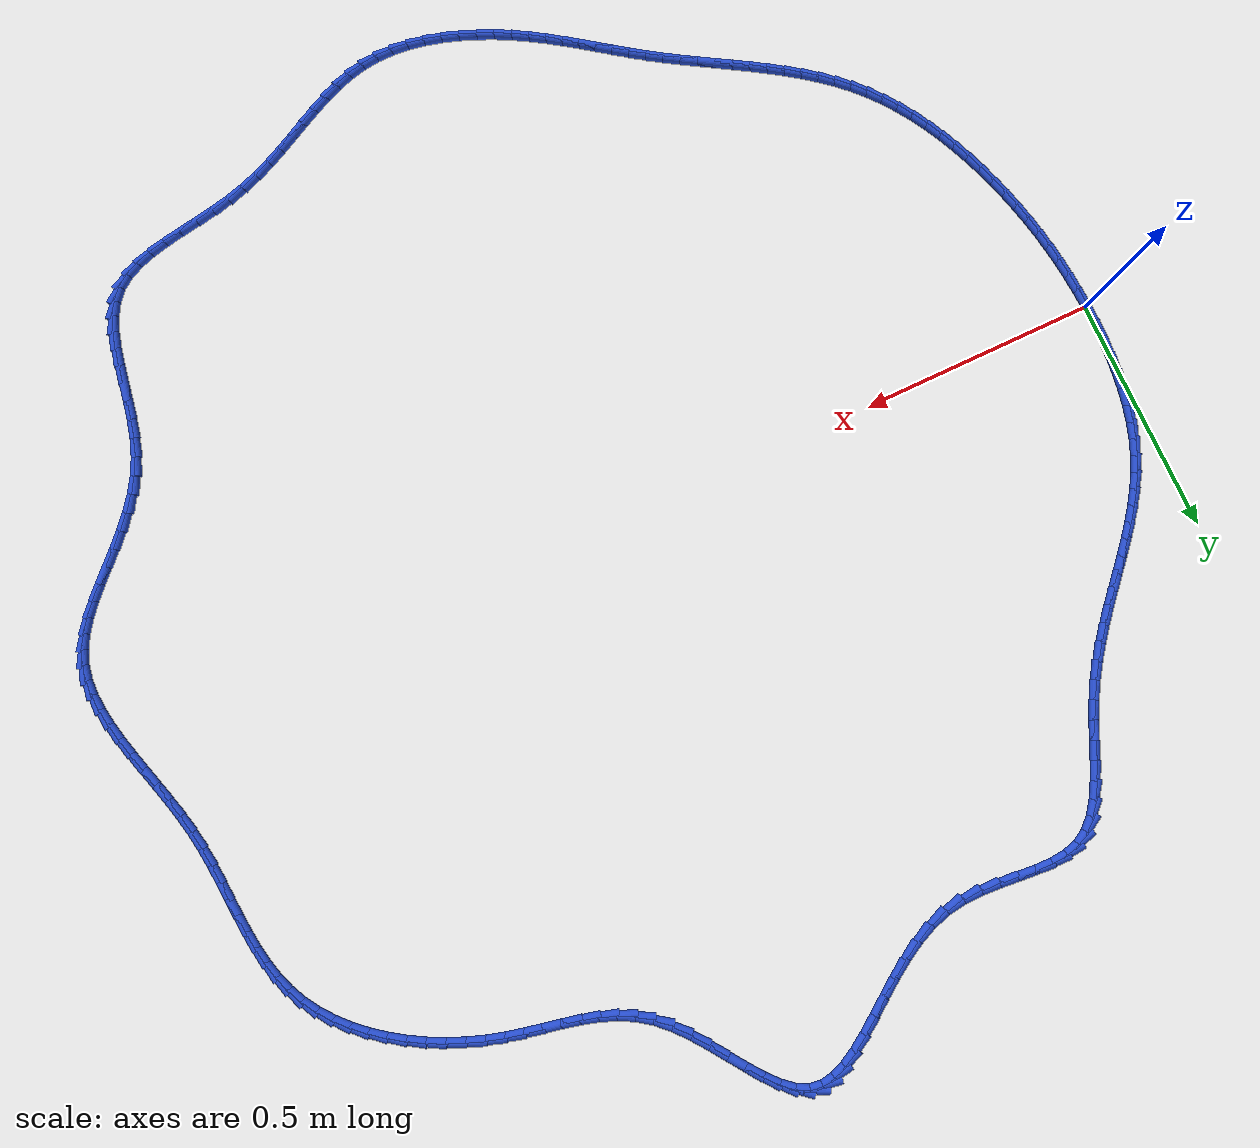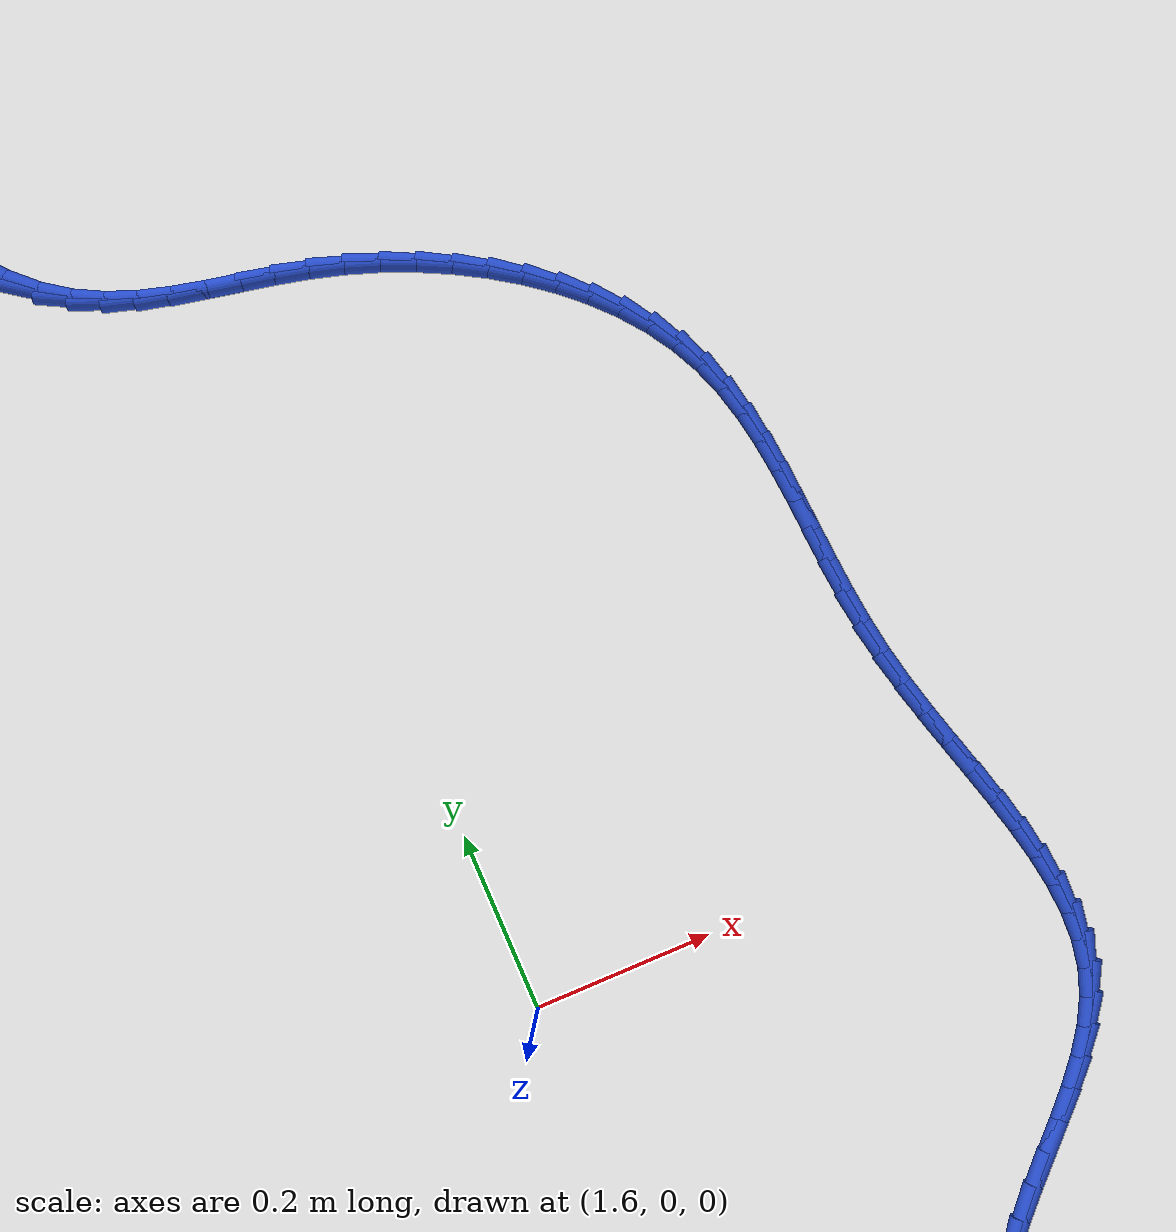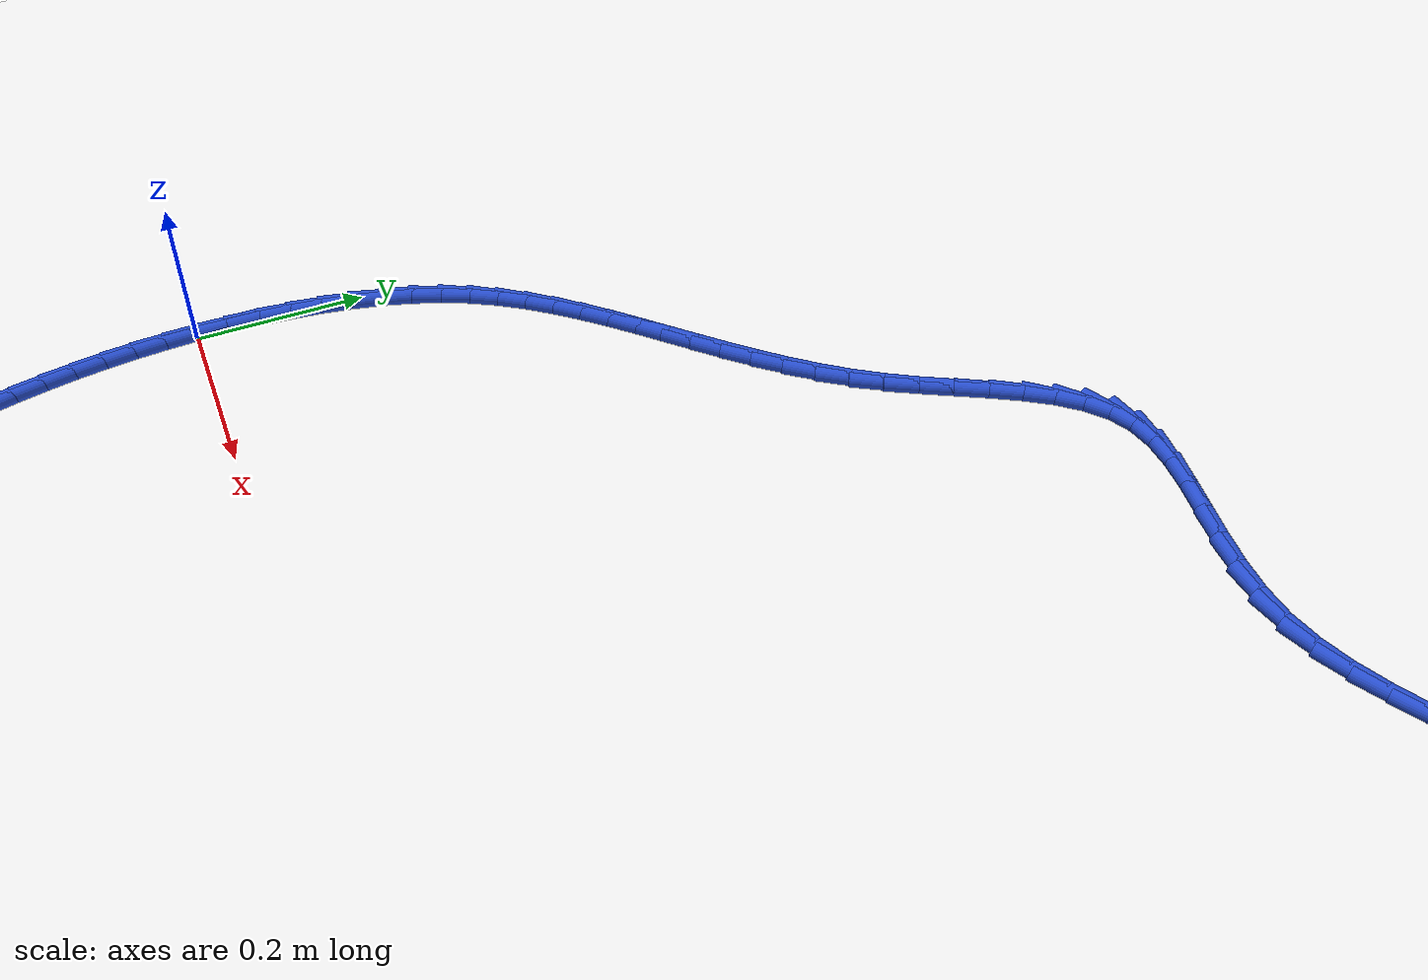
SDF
<sdf version="1.6">
 <world name="default">
  <light name="sun" type="directional">
   <pose>0 0 10 0 -0 0</pose>
   <diffuse>0.8 0.8 0.8 1</diffuse>
   <specular>0.2 0.2 0.2 1</specular>
   <attenuation>
    <range>1000</range>
    <constant>0.9</constant>
    <linear>0.01</linear>
    <quadratic>0.001</quadratic>
   </attenuation>
   <direction>-0.5 0.1 -0.9</direction>
  </light>
  <model name="ground_plane">
   <static>1</static>
   <link name="link">
    <collision name="collision">
     <geometry><plane><normal>0 0 1</normal><size>100 100</size></plane></geometry>
     <surface><friction><ode><mu>100</mu><mu2>50</mu2></ode></friction></surface>
    </collision>
    <visual name="visual">
     <cast_shadows>0</cast_shadows>
     <geometry><plane><normal>0 0 1</normal><size>100 100</size></plane></geometry>
     <material>
      <script><uri>file://media/materials/scripts/gazebo.material</uri><name>Gazebo/WhiteGlow</name></script>
     </material>
    </visual>
   </link>
  </model>
  <gravity>0 0 -9.8</gravity>
  <magnetic_field>6e-06 2.3e-05 -4.2e-05</magnetic_field>
  <atmosphere type="adiabatic"/>
  <physics name="default_physics" default="0" type="ode">
   <max_step_size>0.001</max_step_size>
   <real_time_factor>1</real_time_factor>
   <real_time_update_rate>1000</real_time_update_rate>
  </physics>
  <scene><ambient>0.4 0.4 0.4 1</ambient><background>0.7 0.7 0.7 1</background><shadows>1</shadows></scene>
  <spherical_coordinates>
   <surface_model>EARTH_WGS84</surface_model>
   <latitude_deg>0</latitude_deg>
   <longitude_deg>0</longitude_deg>
   <elevation>0</elevation>
   <heading_deg>0</heading_deg>
  </spherical_coordinates>
  <model name="line">
   <link name="link_0">
    <pose>2.6020852139652106e-17 -9.71445146547012e-17 0.01 0 1.57 -1.5621831902232952</pose>
    <collision name="collision">
     <geometry><cylinder><radius>0.01</radius><length>0.08</length></cylinder></geometry>
    </collision>
    <visual name="visual">
     <material>
      <script><name>Gazebo/Blue</name><uri>file://media/materials/scripts/gazebo.material</uri></script>
     </material>
     <geometry><cylinder><radius>0.01</radius><length>0.08</length></cylinder></geometry>
    </visual>
   </link>
   <link name="link_1">
    <pose>-0.00031968977856093643 0.03711561640169112 0.01 0 1.57 1.5464420975467457</pose>
    <collision name="collision">
     <geometry><cylinder><radius>0.01</radius><length>0.08</length></cylinder></geometry>
    </collision>
    <visual name="visual">
     <material>
      <script><name>Gazebo/Blue</name><uri>file://media/materials/scripts/gazebo.material</uri></script>
     </material>
     <geometry><cylinder><radius>0.01</radius><length>0.08</length></cylinder></geometry>
    </visual>
   </link>
   <link name="link_2">
    <pose>0.0005880509570765188 0.07438065362917015 0.01 0 1.57 1.509807310604159</pose>
    <collision name="collision">
     <geometry><cylinder><radius>0.01</radius><length>0.08</length></cylinder></geometry>
    </collision>
    <visual name="visual">
     <material>
      <script><name>Gazebo/Blue</name><uri>file://media/materials/scripts/gazebo.material</uri></script>
     </material>
     <geometry><cylinder><radius>0.01</radius><length>0.08</length></cylinder></geometry>
    </visual>
   </link>
   <link name="link_3">
    <pose>0.002859856134426444 0.11158387216424501 0.01 0 1.57 1.4689970682819233</pose>
    <collision name="collision">
     <geometry><cylinder><radius>0.01</radius><length>0.08</length></cylinder></geometry>
    </collision>
    <visual name="visual">
     <material>
      <script><name>Gazebo/Blue</name><uri>file://media/materials/scripts/gazebo.material</uri></script>
     </material>
     <geometry><cylinder><radius>0.01</radius><length>0.08</length></cylinder></geometry>
    </visual>
   </link>
   <link name="link_4">
    <pose>0.006632359681002883 0.14851403248872366 0.01 0 1.57 1.4234374467433104</pose>
    <collision name="collision">
     <geometry><cylinder><radius>0.01</radius><length>0.08</length></cylinder></geometry>
    </collision>
    <visual name="visual">
     <material>
      <script><name>Gazebo/Blue</name><uri>file://media/materials/scripts/gazebo.material</uri></script>
     </material>
     <geometry><cylinder><radius>0.01</radius><length>0.08</length></cylinder></geometry>
    </visual>
   </link>
   <link name="link_5">
    <pose>0.012042195524319888 0.18495989508441416 0.01 0 1.57 1.3724935437011863</pose>
    <collision name="collision">
     <geometry><cylinder><radius>0.01</radius><length>0.08</length></cylinder></geometry>
    </collision>
    <visual name="visual">
     <material>
      <script><name>Gazebo/Blue</name><uri>file://media/materials/scripts/gazebo.material</uri></script>
     </material>
     <geometry><cylinder><radius>0.01</radius><length>0.08</length></cylinder></geometry>
    </visual>
   </link>
   <link name="link_6">
    <pose>0.01922599759189152 0.22071022043312447 0.01 0 1.57 1.3154854739663269</pose>
    <collision name="collision">
     <geometry><cylinder><radius>0.01</radius><length>0.08</length></cylinder></geometry>
    </collision>
    <visual name="visual">
     <material>
      <script><name>Gazebo/Blue</name><uri>file://media/materials/scripts/gazebo.material</uri></script>
     </material>
     <geometry><cylinder><radius>0.01</radius><length>0.08</length></cylinder></geometry>
    </visual>
   </link>
   <link name="link_7">
    <pose>0.02832039981123179 0.2555537690166625 0.01 0 1.57 1.2517222985318488</pose>
    <collision name="collision">
     <geometry><cylinder><radius>0.01</radius><length>0.08</length></cylinder></geometry>
    </collision>
    <visual name="visual">
     <material>
      <script><name>Gazebo/Blue</name><uri>file://media/materials/scripts/gazebo.material</uri></script>
     </material>
     <geometry><cylinder><radius>0.01</radius><length>0.08</length></cylinder></geometry>
    </visual>
   </link>
   <link name="link_8">
    <pose>0.0394620361098548 0.2892793013168364 0.01 0 1.57 1.180562507635391</pose>
    <collision name="collision">
     <geometry><cylinder><radius>0.01</radius><length>0.08</length></cylinder></geometry>
    </collision>
    <visual name="visual">
     <material>
      <script><name>Gazebo/Blue</name><uri>file://media/materials/scripts/gazebo.material</uri></script>
     </material>
     <geometry><cylinder><radius>0.01</radius><length>0.08</length></cylinder></geometry>
    </visual>
   </link>
   <link name="link_9">
    <pose>0.05278754041527457 0.32167557781545414 0.01 0 1.57 1.1036009828839137</pose>
    <collision name="collision">
     <geometry><cylinder><radius>0.01</radius><length>0.08</length></cylinder></geometry>
    </collision>
    <visual name="visual">
     <material>
      <script><name>Gazebo/Blue</name><uri>file://media/materials/scripts/gazebo.material</uri></script>
     </material>
     <geometry><cylinder><radius>0.01</radius><length>0.08</length></cylinder></geometry>
    </visual>
   </link>
   <link name="link_10">
    <pose>0.06838152044542657 0.35258886909075804 0.01 0 1.57 1.03238909465765</pose>
    <collision name="collision">
     <geometry><cylinder><radius>0.01</radius><length>0.08</length></cylinder></geometry>
    </collision>
    <visual name="visual">
     <material>
      <script><name>Gazebo/Blue</name><uri>file://media/materials/scripts/gazebo.material</uri></script>
     </material>
     <geometry><cylinder><radius>0.01</radius><length>0.08</length></cylinder></geometry>
    </visual>
   </link>
   <link name="link_11">
    <pose>0.0860508248733353 0.3821724823009723 0.01 0 1.57 0.9718745766253265</pose>
    <collision name="collision">
     <geometry><cylinder><radius>0.01</radius><length>0.08</length></cylinder></geometry>
    </collision>
    <visual name="visual">
     <material>
      <script><name>Gazebo/Blue</name><uri>file://media/materials/scripts/gazebo.material</uri></script>
     </material>
     <geometry><cylinder><radius>0.01</radius><length>0.08</length></cylinder></geometry>
    </visual>
   </link>
   <link name="link_12">
    <pose>0.10550998516170162 0.4106817726241794 0.01 0 1.57 0.9227875499274827</pose>
    <collision name="collision">
     <geometry><cylinder><radius>0.01</radius><length>0.08</length></cylinder></geometry>
    </collision>
    <visual name="visual">
     <material>
      <script><name>Gazebo/Blue</name><uri>file://media/materials/scripts/gazebo.material</uri></script>
     </material>
     <geometry><cylinder><radius>0.01</radius><length>0.08</length></cylinder></geometry>
    </visual>
   </link>
   <link name="link_13">
    <pose>0.12647347104322018 0.4383721634751966 0.01 0 1.57 0.8853421768963635</pose>
    <collision name="collision">
     <geometry><cylinder><radius>0.01</radius><length>0.08</length></cylinder></geometry>
    </collision>
    <visual name="visual">
     <material>
      <script><name>Gazebo/Blue</name><uri>file://media/materials/scripts/gazebo.material</uri></script>
     </material>
     <geometry><cylinder><radius>0.01</radius><length>0.08</length></cylinder></geometry>
    </visual>
   </link>
   <link name="link_14">
    <pose>0.14865575225058542 0.4654990782688404 0.01 0 1.57 0.8594262456779417</pose>
    <collision name="collision">
     <geometry><cylinder><radius>0.01</radius><length>0.08</length></cylinder></geometry>
    </collision>
    <visual name="visual">
     <material>
      <script><name>Gazebo/Blue</name><uri>file://media/materials/scripts/gazebo.material</uri></script>
     </material>
     <geometry><cylinder><radius>0.01</radius><length>0.08</length></cylinder></geometry>
    </visual>
   </link>
   <link name="link_15">
    <pose>0.17177129851649212 0.49231794041992805 0.01 0 1.57 0.8447580056597066</pose>
    <collision name="collision">
     <geometry><cylinder><radius>0.01</radius><length>0.08</length></cylinder></geometry>
    </collision>
    <visual name="visual">
     <material>
      <script><name>Gazebo/Blue</name><uri>file://media/materials/scripts/gazebo.material</uri></script>
     </material>
     <geometry><cylinder><radius>0.01</radius><length>0.08</length></cylinder></geometry>
    </visual>
   </link>
   <link name="link_16">
    <pose>0.19553457957363465 0.5190841733432762 0.01 0 1.57 0.8409933954790574</pose>
    <collision name="collision">
     <geometry><cylinder><radius>0.01</radius><length>0.08</length></cylinder></geometry>
    </collision>
    <visual name="visual">
     <material>
      <script><name>Gazebo/Blue</name><uri>file://media/materials/scripts/gazebo.material</uri></script>
     </material>
     <geometry><cylinder><radius>0.01</radius><length>0.08</length></cylinder></geometry>
    </visual>
   </link>
   <link name="link_17">
    <pose>0.2196600651547077 0.5460532004537018 0.01 0 1.57 0.8477831536583295</pose>
    <collision name="collision">
     <geometry><cylinder><radius>0.01</radius><length>0.08</length></cylinder></geometry>
    </collision>
    <visual name="visual">
     <material>
      <script><name>Gazebo/Blue</name><uri>file://media/materials/scripts/gazebo.material</uri></script>
     </material>
     <geometry><cylinder><radius>0.01</radius><length>0.08</length></cylinder></geometry>
    </visual>
   </link>
   <link name="link_18">
    <pose>0.24386222499240576 0.5734804451660215 0.01 0 1.57 0.8647868487878555</pose>
    <collision name="collision">
     <geometry><cylinder><radius>0.01</radius><length>0.08</length></cylinder></geometry>
    </collision>
    <visual name="visual">
     <material>
      <script><name>Gazebo/Blue</name><uri>file://media/materials/scripts/gazebo.material</uri></script>
     </material>
     <geometry><cylinder><radius>0.01</radius><length>0.08</length></cylinder></geometry>
    </visual>
   </link>
   <link name="link_19">
    <pose>0.2678555288194233 0.6016213308950522 0.01 0 1.57 0.8916521265940476</pose>
    <collision name="collision">
     <geometry><cylinder><radius>0.01</radius><length>0.08</length></cylinder></geometry>
    </collision>
    <visual name="visual">
     <material>
      <script><name>Gazebo/Blue</name><uri>file://media/materials/scripts/gazebo.material</uri></script>
     </material>
     <geometry><cylinder><radius>0.01</radius><length>0.08</length></cylinder></geometry>
    </visual>
   </link>
   <link name="link_20">
    <pose>0.2913544463684551 0.6307312810556109 0.01 0 1.57 0.9279670571064371</pose>
    <collision name="collision">
     <geometry><cylinder><radius>0.01</radius><length>0.08</length></cylinder></geometry>
    </collision>
    <visual name="visual">
     <material>
      <script><name>Gazebo/Blue</name><uri>file://media/materials/scripts/gazebo.material</uri></script>
     </material>
     <geometry><cylinder><radius>0.01</radius><length>0.08</length></cylinder></geometry>
    </visual>
   </link>
   <link name="link_21">
    <pose>0.31407344737219567 0.6610657190625147 0.01 0 1.57 0.9731942881148808</pose>
    <collision name="collision">
     <geometry><cylinder><radius>0.01</radius><length>0.08</length></cylinder></geometry>
    </collision>
    <visual name="visual">
     <material>
      <script><name>Gazebo/Blue</name><uri>file://media/materials/scripts/gazebo.material</uri></script>
     </material>
     <geometry><cylinder><radius>0.01</radius><length>0.08</length></cylinder></geometry>
    </visual>
   </link>
   <link name="link_22">
    <pose>0.3357270015633396 0.6928800683305802 0.01 0 1.57 1.0265989722636952</pose>
    <collision name="collision">
     <geometry><cylinder><radius>0.01</radius><length>0.08</length></cylinder></geometry>
    </collision>
    <visual name="visual">
     <material>
      <script><name>Gazebo/Blue</name><uri>file://media/materials/scripts/gazebo.material</uri></script>
     </material>
     <geometry><cylinder><radius>0.01</radius><length>0.08</length></cylinder></geometry>
    </visual>
   </link>
   <link name="link_23">
    <pose>0.3560295786745813 0.726429752274624 0.01 0 1.57 1.0840526726214288</pose>
    <collision name="collision">
     <geometry><cylinder><radius>0.01</radius><length>0.08</length></cylinder></geometry>
    </collision>
    <visual name="visual">
     <material>
      <script><name>Gazebo/Blue</name><uri>file://media/materials/scripts/gazebo.material</uri></script>
     </material>
     <geometry><cylinder><radius>0.01</radius><length>0.08</length></cylinder></geometry>
    </visual>
   </link>
   <link name="link_24">
    <pose>0.37477418977687776 0.7618495649350913 0.01 0 1.57 1.1207140324198142</pose>
    <collision name="collision">
     <geometry><cylinder><radius>0.01</radius><length>0.08</length></cylinder></geometry>
    </collision>
    <visual name="visual">
     <material>
      <script><name>Gazebo/Blue</name><uri>file://media/materials/scripts/gazebo.material</uri></script>
     </material>
     <geometry><cylinder><radius>0.01</radius><length>0.08</length></cylinder></geometry>
    </visual>
   </link>
   <link name="link_25">
    <pose>0.39238662929740226 0.7983024266606588 0.01 0 1.57 1.1267578113163133</pose>
    <collision name="collision">
     <geometry><cylinder><radius>0.01</radius><length>0.08</length></cylinder></geometry>
    </collision>
    <visual name="visual">
     <material>
      <script><name>Gazebo/Blue</name><uri>file://media/materials/scripts/gazebo.material</uri></script>
     </material>
     <geometry><cylinder><radius>0.01</radius><length>0.08</length></cylinder></geometry>
    </visual>
   </link>
   <link name="link_26">
    <pose>0.4095981545500886 0.834482106169295 0.01 0 1.57 1.1014943201288458</pose>
    <collision name="collision">
     <geometry><cylinder><radius>0.01</radius><length>0.08</length></cylinder></geometry>
    </collision>
    <visual name="visual">
     <material>
      <script><name>Gazebo/Blue</name><uri>file://media/materials/scripts/gazebo.material</uri></script>
     </material>
     <geometry><cylinder><radius>0.01</radius><length>0.08</length></cylinder></geometry>
    </visual>
   </link>
   <link name="link_27">
    <pose>0.42714199902810224 0.8690793370223263 0.01 0 1.57 1.0400313228265887</pose>
    <collision name="collision">
     <geometry><cylinder><radius>0.01</radius><length>0.08</length></cylinder></geometry>
    </collision>
    <visual name="visual">
     <material>
      <script><name>Gazebo/Blue</name><uri>file://media/materials/scripts/gazebo.material</uri></script>
     </material>
     <geometry><cylinder><radius>0.01</radius><length>0.08</length></cylinder></geometry>
    </visual>
   </link>
   <link name="link_28">
    <pose>0.44575139622460985 0.9007848527810798 0.01 0 1.57 0.9324391531395965</pose>
    <collision name="collision">
     <geometry><cylinder><radius>0.01</radius><length>0.08</length></cylinder></geometry>
    </collision>
    <visual name="visual">
     <material>
      <script><name>Gazebo/Blue</name><uri>file://media/materials/scripts/gazebo.material</uri></script>
     </material>
     <geometry><cylinder><radius>0.01</radius><length>0.08</length></cylinder></geometry>
    </visual>
   </link>
   <link name="link_29">
    <pose>0.46615957963277754 0.9282893870068827 0.01 0 1.57 0.7643502515814047</pose>
    <collision name="collision">
     <geometry><cylinder><radius>0.01</radius><length>0.08</length></cylinder></geometry>
    </collision>
    <visual name="visual">
     <material>
      <script><name>Gazebo/Blue</name><uri>file://media/materials/scripts/gazebo.material</uri></script>
     </material>
     <geometry><cylinder><radius>0.01</radius><length>0.08</length></cylinder></geometry>
    </visual>
   </link>
   <link name="link_30">
    <pose>0.4890997827457713 0.9502836732610612 0.01 0 1.57 0.5253221587768561</pose>
    <collision name="collision">
     <geometry><cylinder><radius>0.01</radius><length>0.08</length></cylinder></geometry>
    </collision>
    <visual name="visual">
     <material>
      <script><name>Gazebo/Blue</name><uri>file://media/materials/scripts/gazebo.material</uri></script>
     </material>
     <geometry><cylinder><radius>0.01</radius><length>0.08</length></cylinder></geometry>
    </visual>
   </link>
   <link name="link_31">
    <pose>0.5153000025689671 0.9654706412750996 0.01 0 1.57 0.26630773554642556</pose>
    <collision name="collision">
     <geometry><cylinder><radius>0.01</radius><length>0.08</length></cylinder></geometry>
    </collision>
    <visual name="visual">
     <material>
      <script><name>Gazebo/Blue</name><uri>file://media/materials/scripts/gazebo.material</uri></script>
     </material>
     <geometry><cylinder><radius>0.01</radius><length>0.08</length></cylinder></geometry>
    </visual>
   </link>
   <link name="link_32">
    <pose>0.5450453296759695 0.9735847828545054 0.01 0 1.57 0.07837363461780061</pose>
    <collision name="collision">
     <geometry><cylinder><radius>0.01</radius><length>0.08</length></cylinder></geometry>
    </collision>
    <visual name="visual">
     <material>
      <script><name>Gazebo/Blue</name><uri>file://media/materials/scripts/gazebo.material</uri></script>
     </material>
     <geometry><cylinder><radius>0.01</radius><length>0.08</length></cylinder></geometry>
    </visual>
   </link>
   <link name="link_33">
    <pose>0.5778478761160633 0.9761609143711619 0.01 0 1.57 -0.03528871126451567</pose>
    <collision name="collision">
     <geometry><cylinder><radius>0.01</radius><length>0.08</length></cylinder></geometry>
    </collision>
    <visual name="visual">
     <material>
      <script><name>Gazebo/Blue</name><uri>file://media/materials/scripts/gazebo.material</uri></script>
     </material>
     <geometry><cylinder><radius>0.01</radius><length>0.08</length></cylinder></geometry>
    </visual>
   </link>
   <link name="link_34">
    <pose>0.6131420147980261 0.9749149124463896 0.01 0 1.57 -0.08982345356024937</pose>
    <collision name="collision">
     <geometry><cylinder><radius>0.01</radius><length>0.08</length></cylinder></geometry>
    </collision>
    <visual name="visual">
     <material>
      <script><name>Gazebo/Blue</name><uri>file://media/materials/scripts/gazebo.material</uri></script>
     </material>
     <geometry><cylinder><radius>0.01</radius><length>0.08</length></cylinder></geometry>
    </visual>
   </link>
   <link name="link_35">
    <pose>0.6503621186306352 0.9715626537015101 0.01 0 1.57 -0.09670611162263286</pose>
    <collision name="collision">
     <geometry><cylinder><radius>0.01</radius><length>0.08</length></cylinder></geometry>
    </collision>
    <visual name="visual">
     <material>
      <script><name>Gazebo/Blue</name><uri>file://media/materials/scripts/gazebo.material</uri></script>
     </material>
     <geometry><cylinder><radius>0.01</radius><length>0.08</length></cylinder></geometry>
    </visual>
   </link>
   <link name="link_36">
    <pose>0.6889425605226688 0.9678200147578444 0.01 0 1.57 -0.06131057070642005</pose>
    <collision name="collision">
     <geometry><cylinder><radius>0.01</radius><length>0.08</length></cylinder></geometry>
    </collision>
    <visual name="visual">
     <material>
      <script><name>Gazebo/Blue</name><uri>file://media/materials/scripts/gazebo.material</uri></script>
     </material>
     <geometry><cylinder><radius>0.01</radius><length>0.08</length></cylinder></geometry>
    </visual>
   </link>
   <link name="link_37">
    <pose>0.7283177133829041 0.9654028722367138 0.01 0 1.57 0.015760405678927884</pose>
    <collision name="collision">
     <geometry><cylinder><radius>0.01</radius><length>0.08</length></cylinder></geometry>
    </collision>
    <visual name="visual">
     <material>
      <script><name>Gazebo/Blue</name><uri>file://media/materials/scripts/gazebo.material</uri></script>
     </material>
     <geometry><cylinder><radius>0.01</radius><length>0.08</length></cylinder></geometry>
    </visual>
   </link>
   <link name="link_38">
    <pose>0.7679219501201188 0.9660271027594396 0.01 0 1.57 0.1361975559223388</pose>
    <collision name="collision">
     <geometry><cylinder><radius>0.01</radius><length>0.08</length></cylinder></geometry>
    </collision>
    <visual name="visual">
     <material>
      <script><name>Gazebo/Blue</name><uri>file://media/materials/scripts/gazebo.material</uri></script>
     </material>
     <geometry><cylinder><radius>0.01</radius><length>0.08</length></cylinder></geometry>
    </visual>
   </link>
   <link name="link_39">
    <pose>0.8071896436430905 0.9714085829473431 0.01 0 1.57 0.28709054770283937</pose>
    <collision name="collision">
     <geometry><cylinder><radius>0.01</radius><length>0.08</length></cylinder></geometry>
    </collision>
    <visual name="visual">
     <material>
      <script><name>Gazebo/Blue</name><uri>file://media/materials/scripts/gazebo.material</uri></script>
     </material>
     <geometry><cylinder><radius>0.01</radius><length>0.08</length></cylinder></geometry>
    </visual>
   </link>
   <link name="link_40">
    <pose>0.8456419973119377 0.9827615244980525 0.01 0 1.57 0.41489379603729176</pose>
    <collision name="collision">
     <geometry><cylinder><radius>0.01</radius><length>0.08</length></cylinder></geometry>
    </collision>
    <visual name="visual">
     <material>
      <script><name>Gazebo/Blue</name><uri>file://media/materials/scripts/gazebo.material</uri></script>
     </material>
     <geometry><cylinder><radius>0.01</radius><length>0.08</length></cylinder></geometry>
    </visual>
   </link>
   <link name="link_41">
    <pose>0.8831494973217845 0.9992821495206946 0.01 0 1.57 0.5089331013523337</pose>
    <collision name="collision">
     <geometry><cylinder><radius>0.01</radius><length>0.08</length></cylinder></geometry>
    </collision>
    <visual name="visual">
     <material>
      <script><name>Gazebo/Blue</name><uri>file://media/materials/scripts/gazebo.material</uri></script>
     </material>
     <geometry><cylinder><radius>0.01</radius><length>0.08</length></cylinder></geometry>
    </visual>
   </link>
   <link name="link_42">
    <pose>0.9196704435988041 1.0196593342796434 0.01 0 1.57 0.5734456332069271</pose>
    <collision name="collision">
     <geometry><cylinder><radius>0.01</radius><length>0.08</length></cylinder></geometry>
    </collision>
    <visual name="visual">
     <material>
      <script><name>Gazebo/Blue</name><uri>file://media/materials/scripts/gazebo.material</uri></script>
     </material>
     <geometry><cylinder><radius>0.01</radius><length>0.08</length></cylinder></geometry>
    </visual>
   </link>
   <link name="link_43">
    <pose>0.9551631360697463 1.0425819550359392 0.01 0 1.57 0.6119146043895051</pose>
    <collision name="collision">
     <geometry><cylinder><radius>0.01</radius><length>0.08</length></cylinder></geometry>
    </collision>
    <visual name="visual">
     <material>
      <script><name>Gazebo/Blue</name><uri>file://media/materials/scripts/gazebo.material</uri></script>
     </material>
     <geometry><cylinder><radius>0.01</radius><length>0.08</length></cylinder></geometry>
    </visual>
   </link>
   <link name="link_44">
    <pose>0.9895858746613619 1.0667388880506217 0.01 0 1.57 0.6259212328232577</pose>
    <collision name="collision">
     <geometry><cylinder><radius>0.01</radius><length>0.08</length></cylinder></geometry>
    </collision>
    <visual name="visual">
     <material>
      <script><name>Gazebo/Blue</name><uri>file://media/materials/scripts/gazebo.material</uri></script>
     </material>
     <geometry><cylinder><radius>0.01</radius><length>0.08</length></cylinder></geometry>
    </visual>
   </link>
   <link name="link_45">
    <pose>1.0228969593004011 1.0908190095847305 0.01 0 1.57 0.6145095918454402</pose>
    <collision name="collision">
     <geometry><cylinder><radius>0.01</radius><length>0.08</length></cylinder></geometry>
    </collision>
    <visual name="visual">
     <material>
      <script><name>Gazebo/Blue</name><uri>file://media/materials/scripts/gazebo.material</uri></script>
     </material>
     <geometry><cylinder><radius>0.01</radius><length>0.08</length></cylinder></geometry>
    </visual>
   </link>
   <link name="link_46">
    <pose>1.0550546899136135 1.1135111958993054 0.01 0 1.57 0.573358446752258</pose>
    <collision name="collision">
     <geometry><cylinder><radius>0.01</radius><length>0.08</length></cylinder></geometry>
    </collision>
    <visual name="visual">
     <material>
      <script><name>Gazebo/Blue</name><uri>file://media/materials/scripts/gazebo.material</uri></script>
     </material>
     <geometry><cylinder><radius>0.01</radius><length>0.08</length></cylinder></geometry>
    </visual>
   </link>
   <link name="link_47">
    <pose>1.086017366427749 1.1335043232553859 0.01 0 1.57 0.4933329701970258</pose>
    <collision name="collision">
     <geometry><cylinder><radius>0.01</radius><length>0.08</length></cylinder></geometry>
    </collision>
    <visual name="visual">
     <material>
      <script><name>Gazebo/Blue</name><uri>file://media/materials/scripts/gazebo.material</uri></script>
     </material>
     <geometry><cylinder><radius>0.01</radius><length>0.08</length></cylinder></geometry>
    </visual>
   </link>
   <link name="link_48">
    <pose>1.1157432887695589 1.1494872679140118 0.01 0 1.57 0.3585807426027486</pose>
    <collision name="collision">
     <geometry><cylinder><radius>0.01</radius><length>0.08</length></cylinder></geometry>
    </collision>
    <visual name="visual">
     <material>
      <script><name>Gazebo/Blue</name><uri>file://media/materials/scripts/gazebo.material</uri></script>
     </material>
     <geometry><cylinder><radius>0.01</radius><length>0.08</length></cylinder></geometry>
    </visual>
   </link>
   <link name="link_49">
    <pose>1.144190756865792 1.1601489061362231 0.01 0 1.57 0.1474515576269231</pose>
    <collision name="collision">
     <geometry><cylinder><radius>0.01</radius><length>0.08</length></cylinder></geometry>
    </collision>
    <visual name="visual">
     <material>
      <script><name>Gazebo/Blue</name><uri>file://media/materials/scripts/gazebo.material</uri></script>
     </material>
     <geometry><cylinder><radius>0.01</radius><length>0.08</length></cylinder></geometry>
    </visual>
   </link>
   <link name="link_50">
    <pose>1.1713180706431996 1.1641781141830592 0.01 0 1.57 -0.15076456251287718</pose>
    <collision name="collision">
     <geometry><cylinder><radius>0.01</radius><length>0.08</length></cylinder></geometry>
    </collision>
    <visual name="visual">
     <material>
      <script><name>Gazebo/Blue</name><uri>file://media/materials/scripts/gazebo.material</uri></script>
     </material>
     <geometry><cylinder><radius>0.01</radius><length>0.08</length></cylinder></geometry>
    </visual>
   </link>
   <link name="link_51">
    <pose>1.1970835482160538 1.1602638914919834 0.01 0 1.57 -0.4751864375075942</pose>
    <collision name="collision">
     <geometry><cylinder><radius>0.01</radius><length>0.08</length></cylinder></geometry>
    </collision>
    <visual name="visual">
     <material>
      <script><name>Gazebo/Blue</name><uri>file://media/materials/scripts/gazebo.material</uri></script>
     </material>
     <geometry><cylinder><radius>0.01</radius><length>0.08</length></cylinder></geometry>
    </visual>
   </link>
   <link name="link_52">
    <pose>1.2215325430095263 1.147684690976005 0.01 0 1.57 -0.7061386202762824</pose>
    <collision name="collision">
     <geometry><cylinder><radius>0.01</radius><length>0.08</length></cylinder></geometry>
    </collision>
    <visual name="visual">
     <material>
      <script><name>Gazebo/Blue</name><uri>file://media/materials/scripts/gazebo.material</uri></script>
     </material>
     <geometry><cylinder><radius>0.01</radius><length>0.08</length></cylinder></geometry>
    </visual>
   </link>
   <link name="link_53">
    <pose>1.244998758751948 1.1276718406124886 0.01 0 1.57 -0.8455970297754193</pose>
    <collision name="collision">
     <geometry><cylinder><radius>0.01</radius><length>0.08</length></cylinder></geometry>
    </collision>
    <visual name="visual">
     <material>
      <script><name>Gazebo/Blue</name><uri>file://media/materials/scripts/gazebo.material</uri></script>
     </material>
     <geometry><cylinder><radius>0.01</radius><length>0.08</length></cylinder></geometry>
    </visual>
   </link>
   <link name="link_54">
    <pose>1.2678755344581336 1.1018605530380166 0.01 0 1.57 -0.9230430249240104</pose>
    <collision name="collision">
     <geometry><cylinder><radius>0.01</radius><length>0.08</length></cylinder></geometry>
    </collision>
    <visual name="visual">
     <material>
      <script><name>Gazebo/Blue</name><uri>file://media/materials/scripts/gazebo.material</uri></script>
     </material>
     <geometry><cylinder><radius>0.01</radius><length>0.08</length></cylinder></geometry>
    </visual>
   </link>
   <link name="link_55">
    <pose>1.2905562091428973 1.071886040889172 0.01 0 1.57 -0.957470338299564</pose>
    <collision name="collision">
     <geometry><cylinder><radius>0.01</radius><length>0.08</length></cylinder></geometry>
    </collision>
    <visual name="visual">
     <material>
      <script><name>Gazebo/Blue</name><uri>file://media/materials/scripts/gazebo.material</uri></script>
     </material>
     <geometry><cylinder><radius>0.01</radius><length>0.08</length></cylinder></geometry>
    </visual>
   </link>
   <link name="link_56">
    <pose>1.3134341218210528 1.039383516802538 0.01 0 1.57 -0.9582285881067983</pose>
    <collision name="collision">
     <geometry><cylinder><radius>0.01</radius><length>0.08</length></cylinder></geometry>
    </collision>
    <visual name="visual">
     <material>
      <script><name>Gazebo/Blue</name><uri>file://media/materials/scripts/gazebo.material</uri></script>
     </material>
     <geometry><cylinder><radius>0.01</radius><length>0.08</length></cylinder></geometry>
    </visual>
   </link>
   <link name="link_57">
    <pose>1.336902611507415 1.0059881934146968 0.01 0 1.57 -0.928026247705119</pose>
    <collision name="collision">
     <geometry><cylinder><radius>0.01</radius><length>0.08</length></cylinder></geometry>
    </collision>
    <visual name="visual">
     <material>
      <script><name>Gazebo/Blue</name><uri>file://media/materials/scripts/gazebo.material</uri></script>
     </material>
     <geometry><cylinder><radius>0.01</radius><length>0.08</length></cylinder></geometry>
    </visual>
   </link>
   <link name="link_58">
    <pose>1.3613550172167972 0.973335283362232 0.01 0 1.57 -0.8644705898778409</pose>
    <collision name="collision">
     <geometry><cylinder><radius>0.01</radius><length>0.08</length></cylinder></geometry>
    </collision>
    <visual name="visual">
     <material>
      <script><name>Gazebo/Blue</name><uri>file://media/materials/scripts/gazebo.material</uri></script>
     </material>
     <geometry><cylinder><radius>0.01</radius><length>0.08</length></cylinder></geometry>
    </visual>
   </link>
   <link name="link_59">
    <pose>1.3871846779640138 0.943059999281726 0.01 0 1.57 -0.7605670192071126</pose>
    <collision name="collision">
     <geometry><cylinder><radius>0.01</radius><length>0.08</length></cylinder></geometry>
    </collision>
    <visual name="visual">
     <material>
      <script><name>Gazebo/Blue</name><uri>file://media/materials/scripts/gazebo.material</uri></script>
     </material>
     <geometry><cylinder><radius>0.01</radius><length>0.08</length></cylinder></geometry>
    </visual>
   </link>
   <link name="link_60">
    <pose>1.4147849201590197 0.9167975054093039 0.01 0 1.57 -0.6189108469968196</pose>
    <collision name="collision">
     <geometry><cylinder><radius>0.01</radius><length>0.08</length></cylinder></geometry>
    </collision>
    <visual name="visual">
     <material>
      <script><name>Gazebo/Blue</name><uri>file://media/materials/scripts/gazebo.material</uri></script>
     </material>
     <geometry><cylinder><radius>0.01</radius><length>0.08</length></cylinder></geometry>
    </visual>
   </link>
   <link name="link_61">
    <pose>1.44442045823639 0.8956891184690687 0.01 0 1.57 -0.48319615100054186</pose>
    <collision name="collision">
     <geometry><cylinder><radius>0.01</radius><length>0.08</length></cylinder></geometry>
    </collision>
    <visual name="visual">
     <material>
      <script><name>Gazebo/Blue</name><uri>file://media/materials/scripts/gazebo.material</uri></script>
     </material>
     <geometry><cylinder><radius>0.01</radius><length>0.08</length></cylinder></geometry>
    </visual>
   </link>
   <link name="link_62">
    <pose>1.475910828601771 0.8791667493436757 0.01 0 1.57 -0.3712610133999536</pose>
    <collision name="collision">
     <geometry><cylinder><radius>0.01</radius><length>0.08</length></cylinder></geometry>
    </collision>
    <visual name="visual">
     <material>
      <script><name>Gazebo/Blue</name><uri>file://media/materials/scripts/gazebo.material</uri></script>
     </material>
     <geometry><cylinder><radius>0.01</radius><length>0.08</length></cylinder></geometry>
    </visual>
   </link>
   <link name="link_63">
    <pose>1.5089793125426583 0.8662927060815383 0.01 0 1.57 -0.28751350593775454</pose>
    <collision name="collision">
     <geometry><cylinder><radius>0.01</radius><length>0.08</length></cylinder></geometry>
    </collision>
    <visual name="visual">
     <material>
      <script><name>Gazebo/Blue</name><uri>file://media/materials/scripts/gazebo.material</uri></script>
     </material>
     <geometry><cylinder><radius>0.01</radius><length>0.08</length></cylinder></geometry>
    </visual>
   </link>
   <link name="link_64">
    <pose>1.543349191346549 0.8561292967310701 0.01 0 1.57 -0.23275881774197626</pose>
    <collision name="collision">
     <geometry><cylinder><radius>0.01</radius><length>0.08</length></cylinder></geometry>
    </collision>
    <visual name="visual">
     <material>
      <script><name>Gazebo/Blue</name><uri>file://media/materials/scripts/gazebo.material</uri></script>
     </material>
     <geometry><cylinder><radius>0.01</radius><length>0.08</length></cylinder></geometry>
    </visual>
   </link>
   <link name="link_65">
    <pose>1.5787437463009388 0.8477388293406846 0.01 0 1.57 -0.2060722092925332</pose>
    <collision name="collision">
     <geometry><cylinder><radius>0.01</radius><length>0.08</length></cylinder></geometry>
    </collision>
    <visual name="visual">
     <material>
      <script><name>Gazebo/Blue</name><uri>file://media/materials/scripts/gazebo.material</uri></script>
     </material>
     <geometry><cylinder><radius>0.01</radius><length>0.08</length></cylinder></geometry>
    </visual>
   </link>
   <link name="link_66">
    <pose>1.6148862586933241 0.8401836119587954 0.01 0 1.57 -0.2061751643010123</pose>
    <collision name="collision">
     <geometry><cylinder><radius>0.01</radius><length>0.08</length></cylinder></geometry>
    </collision>
    <visual name="visual">
     <material>
      <script><name>Gazebo/Blue</name><uri>file://media/materials/scripts/gazebo.material</uri></script>
     </material>
     <geometry><cylinder><radius>0.01</radius><length>0.08</length></cylinder></geometry>
    </visual>
   </link>
   <link name="link_67">
    <pose>1.6515000098112014 0.8325259526338161 0.01 0 1.57 -0.23204353583484988</pose>
    <collision name="collision">
     <geometry><cylinder><radius>0.01</radius><length>0.08</length></cylinder></geometry>
    </collision>
    <visual name="visual">
     <material>
      <script><name>Gazebo/Blue</name><uri>file://media/materials/scripts/gazebo.material</uri></script>
     </material>
     <geometry><cylinder><radius>0.01</radius><length>0.08</length></cylinder></geometry>
    </visual>
   </link>
   <link name="link_68">
    <pose>1.688308280942067 0.8238281594141602 0.01 0 1.57 -0.28190662828971097</pose>
    <collision name="collision">
     <geometry><cylinder><radius>0.01</radius><length>0.08</length></cylinder></geometry>
    </collision>
    <visual name="visual">
     <material>
      <script><name>Gazebo/Blue</name><uri>file://media/materials/scripts/gazebo.material</uri></script>
     </material>
     <geometry><cylinder><radius>0.01</radius><length>0.08</length></cylinder></geometry>
    </visual>
   </link>
   <link name="link_69">
    <pose>1.725032950814366 0.8131919699556586 0.01 0 1.57 -0.34136410213897567</pose>
    <collision name="collision">
     <geometry><cylinder><radius>0.01</radius><length>0.08</length></cylinder></geometry>
    </collision>
    <visual name="visual">
     <material>
      <script><name>Gazebo/Blue</name><uri>file://media/materials/scripts/gazebo.material</uri></script>
     </material>
     <geometry><cylinder><radius>0.01</radius><length>0.08</length></cylinder></geometry>
    </visual>
   </link>
   <link name="link_70">
    <pose>1.761375936016205 0.80028030994824 0.01 0 1.57 -0.4008228046986829</pose>
    <collision name="collision">
     <geometry><cylinder><radius>0.01</radius><length>0.08</length></cylinder></geometry>
    </collision>
    <visual name="visual">
     <material>
      <script><name>Gazebo/Blue</name><uri>file://media/materials/scripts/gazebo.material</uri></script>
     </material>
     <geometry><cylinder><radius>0.01</radius><length>0.08</length></cylinder></geometry>
    </visual>
   </link>
   <link name="link_71">
    <pose>1.7970242938261642 0.7851738391805707 0.01 0 1.57 -0.46111446925910105</pose>
    <collision name="collision">
     <geometry><cylinder><radius>0.01</radius><length>0.08</length></cylinder></geometry>
    </collision>
    <visual name="visual">
     <material>
      <script><name>Gazebo/Blue</name><uri>file://media/materials/scripts/gazebo.material</uri></script>
     </material>
     <geometry><cylinder><radius>0.01</radius><length>0.08</length></cylinder></geometry>
    </visual>
   </link>
   <link name="link_72">
    <pose>1.8316647274926778 0.7679631701556641 0.01 0 1.57 -0.5233150710984057</pose>
    <collision name="collision">
     <geometry><cylinder><radius>0.01</radius><length>0.08</length></cylinder></geometry>
    </collision>
    <visual name="visual">
     <material>
      <script><name>Gazebo/Blue</name><uri>file://media/materials/scripts/gazebo.material</uri></script>
     </material>
     <geometry><cylinder><radius>0.01</radius><length>0.08</length></cylinder></geometry>
    </visual>
   </link>
   <link name="link_73">
    <pose>1.86498394026418 0.7487389153765343 0.01 0 1.57 -0.5885289566761714</pose>
    <collision name="collision">
     <geometry><cylinder><radius>0.01</radius><length>0.08</length></cylinder></geometry>
    </collision>
    <visual name="visual">
     <material>
      <script><name>Gazebo/Blue</name><uri>file://media/materials/scripts/gazebo.material</uri></script>
     </material>
     <geometry><cylinder><radius>0.01</radius><length>0.08</length></cylinder></geometry>
    </visual>
   </link>
   <link name="link_74">
    <pose>1.8966686353891054 0.727591687346194 0.01 0 1.57 -0.6579115562683078</pose>
    <collision name="collision">
     <geometry><cylinder><radius>0.01</radius><length>0.08</length></cylinder></geometry>
    </collision>
    <visual name="visual">
     <material>
      <script><name>Gazebo/Blue</name><uri>file://media/materials/scripts/gazebo.material</uri></script>
     </material>
     <geometry><cylinder><radius>0.01</radius><length>0.08</length></cylinder></geometry>
    </visual>
   </link>
   <link name="link_75">
    <pose>1.9264055161158897 0.7046120985676574 0.01 0 1.57 -0.7326772315131554</pose>
    <collision name="collision">
     <geometry><cylinder><radius>0.01</radius><length>0.08</length></cylinder></geometry>
    </collision>
    <visual name="visual">
     <material>
      <script><name>Gazebo/Blue</name><uri>file://media/materials/scripts/gazebo.material</uri></script>
     </material>
     <geometry><cylinder><radius>0.01</radius><length>0.08</length></cylinder></geometry>
    </visual>
   </link>
   <link name="link_76">
    <pose>1.953881285692966 0.6798907615439381 0.01 0 1.57 -0.8140815579215152</pose>
    <collision name="collision">
     <geometry><cylinder><radius>0.01</radius><length>0.08</length></cylinder></geometry>
    </collision>
    <visual name="visual">
     <material>
      <script><name>Gazebo/Blue</name><uri>file://media/materials/scripts/gazebo.material</uri></script>
     </material>
     <geometry><cylinder><radius>0.01</radius><length>0.08</length></cylinder></geometry>
    </visual>
   </link>
   <link name="link_77">
    <pose>1.9787826473687704 0.6535182887780493 0.01 0 1.57 -0.9033611643385854</pose>
    <collision name="collision">
     <geometry><cylinder><radius>0.01</radius><length>0.08</length></cylinder></geometry>
    </collision>
    <visual name="visual">
     <material>
      <script><name>Gazebo/Blue</name><uri>file://media/materials/scripts/gazebo.material</uri></script>
     </material>
     <geometry><cylinder><radius>0.01</radius><length>0.08</length></cylinder></geometry>
    </visual>
   </link>
   <link name="link_78">
    <pose>2.000796304391737 0.6255852927730049 0.01 0 1.57 -1.0016087225236967</pose>
    <collision name="collision">
     <geometry><cylinder><radius>0.01</radius><length>0.08</length></cylinder></geometry>
    </collision>
    <visual name="visual">
     <material>
      <script><name>Gazebo/Blue</name><uri>file://media/materials/scripts/gazebo.material</uri></script>
     </material>
     <geometry><cylinder><radius>0.01</radius><length>0.08</length></cylinder></geometry>
    </visual>
   </link>
   <link name="link_79">
    <pose>2.0196089600103 0.596182386031818 0.01 0 1.57 -1.1094890124063956</pose>
    <collision name="collision">
     <geometry><cylinder><radius>0.01</radius><length>0.08</length></cylinder></geometry>
    </collision>
    <visual name="visual">
     <material>
      <script><name>Gazebo/Blue</name><uri>file://media/materials/scripts/gazebo.material</uri></script>
     </material>
     <geometry><cylinder><radius>0.01</radius><length>0.08</length></cylinder></geometry>
    </visual>
   </link>
   <link name="link_80">
    <pose>2.03491007702347 0.5654002640870707 0.01 0 1.57 -1.2189053734407655</pose>
    <collision name="collision">
     <geometry><cylinder><radius>0.01</radius><length>0.08</length></cylinder></geometry>
    </collision>
    <visual name="visual">
     <material>
      <script><name>Gazebo/Blue</name><uri>file://media/materials/scripts/gazebo.material</uri></script>
     </material>
     <geometry><cylinder><radius>0.01</radius><length>0.08</length></cylinder></geometry>
    </visual>
   </link>
   <link name="link_81">
    <pose>2.0466823082459062 0.5333384439948475 0.01 0 1.57 -1.3125950378642746</pose>
    <collision name="collision">
     <geometry><cylinder><radius>0.01</radius><length>0.08</length></cylinder></geometry>
    </collision>
    <visual name="visual">
     <material>
      <script><name>Gazebo/Blue</name><uri>file://media/materials/scripts/gazebo.material</uri></script>
     </material>
     <geometry><cylinder><radius>0.01</radius><length>0.08</length></cylinder></geometry>
    </visual>
   </link>
   <link name="link_82">
    <pose>2.0554570427227237 0.500112953228699 0.01 0 1.57 -1.3870553838406703</pose>
    <collision name="collision">
     <geometry><cylinder><radius>0.01</radius><length>0.08</length></cylinder></geometry>
    </collision>
    <visual name="visual">
     <material>
      <script><name>Gazebo/Blue</name><uri>file://media/materials/scripts/gazebo.material</uri></script>
     </material>
     <geometry><cylinder><radius>0.01</radius><length>0.08</length></cylinder></geometry>
    </visual>
   </link>
   <link name="link_83">
    <pose>2.061825922090857 0.46584163214674285 0.01 0 1.57 -1.4421148878440995</pose>
    <collision name="collision">
     <geometry><cylinder><radius>0.01</radius><length>0.08</length></cylinder></geometry>
    </collision>
    <visual name="visual">
     <material>
      <script><name>Gazebo/Blue</name><uri>file://media/materials/scripts/gazebo.material</uri></script>
     </material>
     <geometry><cylinder><radius>0.01</radius><length>0.08</length></cylinder></geometry>
    </visual>
   </link>
   <link name="link_84">
    <pose>2.0663805879872403 0.4306423211070963 0.01 0 1.57 -1.4785252347413949</pose>
    <collision name="collision">
     <geometry><cylinder><radius>0.01</radius><length>0.08</length></cylinder></geometry>
    </collision>
    <visual name="visual">
     <material>
      <script><name>Gazebo/Blue</name><uri>file://media/materials/scripts/gazebo.material</uri></script>
     </material>
     <geometry><cylinder><radius>0.01</radius><length>0.08</length></cylinder></geometry>
    </visual>
   </link>
   <link name="link_85">
    <pose>2.0697126820488077 0.39463286046787743 0.01 0 1.57 -1.497331134022991</pose>
    <collision name="collision">
     <geometry><cylinder><radius>0.01</radius><length>0.08</length></cylinder></geometry>
    </collision>
    <visual name="visual">
     <material>
      <script><name>Gazebo/Blue</name><uri>file://media/materials/scripts/gazebo.material</uri></script>
     </material>
     <geometry><cylinder><radius>0.01</radius><length>0.08</length></cylinder></geometry>
    </visual>
   </link>
   <link name="link_86">
    <pose>2.072413845912495 0.3579310905872047 0.01 0 1.57 -1.4995078972231164</pose>
    <collision name="collision">
     <geometry><cylinder><radius>0.01</radius><length>0.08</length></cylinder></geometry>
    </collision>
    <visual name="visual">
     <material>
      <script><name>Gazebo/Blue</name><uri>file://media/materials/scripts/gazebo.material</uri></script>
     </material>
     <geometry><cylinder><radius>0.01</radius><length>0.08</length></cylinder></geometry>
    </visual>
   </link>
   <link name="link_87">
    <pose>2.075075721215234 0.32065485182319464 0.01 0 1.57 -1.485817690421677</pose>
    <collision name="collision">
     <geometry><cylinder><radius>0.01</radius><length>0.08</length></cylinder></geometry>
    </collision>
    <visual name="visual">
     <material>
      <script><name>Gazebo/Blue</name><uri>file://media/materials/scripts/gazebo.material</uri></script>
     </material>
     <geometry><cylinder><radius>0.01</radius><length>0.08</length></cylinder></geometry>
    </visual>
   </link>
   <link name="link_88">
    <pose>2.0782899495939624 0.282921984533966 0.01 0 1.57 -1.456818247511328</pose>
    <collision name="collision">
     <geometry><cylinder><radius>0.01</radius><length>0.08</length></cylinder></geometry>
    </collision>
    <visual name="visual">
     <material>
      <script><name>Gazebo/Blue</name><uri>file://media/materials/scripts/gazebo.material</uri></script>
     </material>
     <geometry><cylinder><radius>0.01</radius><length>0.08</length></cylinder></geometry>
    </visual>
   </link>
   <link name="link_89">
    <pose>2.0826481726856128 0.24485032907763626 0.01 0 1.57 -1.412980651369111</pose>
    <collision name="collision">
     <geometry><cylinder><radius>0.01</radius><length>0.08</length></cylinder></geometry>
    </collision>
    <visual name="visual">
     <material>
      <script><name>Gazebo/Blue</name><uri>file://media/materials/scripts/gazebo.material</uri></script>
     </material>
     <geometry><cylinder><radius>0.01</radius><length>0.08</length></cylinder></geometry>
    </visual>
   </link>
   <link name="link_90">
    <pose>2.0887420205853138 0.2065577260763874 0.01 0 1.57 -1.3606827715645198</pose>
    <collision name="collision">
     <geometry><cylinder><radius>0.01</radius><length>0.08</length></cylinder></geometry>
    </collision>
    <visual name="visual">
     <material>
      <script><name>Gazebo/Blue</name><uri>file://media/materials/scripts/gazebo.material</uri></script>
     </material>
     <geometry><cylinder><radius>0.01</radius><length>0.08</length></cylinder></geometry>
    </visual>
   </link>
   <link name="link_91">
    <pose>2.096929192883644 0.16816736821804593 0.01 0 1.57 -1.3205020482886705</pose>
    <collision name="collision">
     <geometry><cylinder><radius>0.01</radius><length>0.08</length></cylinder></geometry>
    </collision>
    <visual name="visual">
     <material>
      <script><name>Gazebo/Blue</name><uri>file://media/materials/scripts/gazebo.material</uri></script>
     </material>
     <geometry><cylinder><radius>0.01</radius><length>0.08</length></cylinder></geometry>
    </visual>
   </link>
   <link name="link_92">
    <pose>2.10673250894313 0.12982154930679857 0.01 0 1.57 -1.2960196539365378</pose>
    <collision name="collision">
     <geometry><cylinder><radius>0.01</radius><length>0.08</length></cylinder></geometry>
    </collision>
    <visual name="visual">
     <material>
      <script><name>Gazebo/Blue</name><uri>file://media/materials/scripts/gazebo.material</uri></script>
     </material>
     <geometry><cylinder><radius>0.01</radius><length>0.08</length></cylinder></geometry>
    </visual>
   </link>
   <link name="link_93">
    <pose>2.11748861350798 0.09166682261175671 0.01 0 1.57 -1.2866231657273888</pose>
    <collision name="collision">
     <geometry><cylinder><radius>0.01</radius><length>0.08</length></cylinder></geometry>
    </collision>
    <visual name="visual">
     <material>
      <script><name>Gazebo/Blue</name><uri>file://media/materials/scripts/gazebo.material</uri></script>
     </material>
     <geometry><cylinder><radius>0.01</radius><length>0.08</length></cylinder></geometry>
    </visual>
   </link>
   <link name="link_94">
    <pose>2.128534151322399 0.05384974140203034 0.01 0 1.57 -1.292370919327129</pose>
    <collision name="collision">
     <geometry><cylinder><radius>0.01</radius><length>0.08</length></cylinder></geometry>
    </collision>
    <visual name="visual">
     <material>
      <script><name>Gazebo/Blue</name><uri>file://media/materials/scripts/gazebo.material</uri></script>
     </material>
     <geometry><cylinder><radius>0.01</radius><length>0.08</length></cylinder></geometry>
    </visual>
   </link>
   <link name="link_95">
    <pose>2.139205767130596 0.016516858946730772 0.01 0 1.57 -1.3140872493059752</pose>
    <collision name="collision">
     <geometry><cylinder><radius>0.01</radius><length>0.08</length></cylinder></geometry>
    </collision>
    <visual name="visual">
     <material>
      <script><name>Gazebo/Blue</name><uri>file://media/materials/scripts/gazebo.material</uri></script>
     </material>
     <geometry><cylinder><radius>0.01</radius><length>0.08</length></cylinder></geometry>
    </visual>
   </link>
   <link name="link_96">
    <pose>2.148840105676777 -0.020185271485031096 0.01 0 1.57 -1.3534431468996282</pose>
    <collision name="collision">
     <geometry><cylinder><radius>0.01</radius><length>0.08</length></cylinder></geometry>
    </collision>
    <visual name="visual">
     <material>
      <script><name>Gazebo/Blue</name><uri>file://media/materials/scripts/gazebo.material</uri></script>
     </material>
     <geometry><cylinder><radius>0.01</radius><length>0.08</length></cylinder></geometry>
    </visual>
   </link>
   <link name="link_97">
    <pose>2.1567738117051496 -0.05611009662414439 0.01 0 1.57 -1.4129890610221878</pose>
    <collision name="collision">
     <geometry><cylinder><radius>0.01</radius><length>0.08</length></cylinder></geometry>
    </collision>
    <visual name="visual">
     <material>
      <script><name>Gazebo/Blue</name><uri>file://media/materials/scripts/gazebo.material</uri></script>
     </material>
     <geometry><cylinder><radius>0.01</radius><length>0.08</length></cylinder></geometry>
    </visual>
   </link>
   <link name="link_98">
    <pose>2.1623435299599203 -0.09111106320149759 0.01 0 1.57 -1.4960072965898743</pose>
    <collision name="collision">
     <geometry><cylinder><radius>0.01</radius><length>0.08</length></cylinder></geometry>
    </collision>
    <visual name="visual">
     <material>
      <script><name>Gazebo/Blue</name><uri>file://media/materials/scripts/gazebo.material</uri></script>
     </material>
     <geometry><cylinder><radius>0.01</radius><length>0.08</length></cylinder></geometry>
    </visual>
   </link>
   <link name="link_99">
    <pose>2.1648859051852964 -0.12504161794798122 0.01 0 1.57 1.5357084084011936</pose>
    <collision name="collision">
     <geometry><cylinder><radius>0.01</radius><length>0.08</length></cylinder></geometry>
    </collision>
    <visual name="visual">
     <material>
      <script><name>Gazebo/Blue</name><uri>file://media/materials/scripts/gazebo.material</uri></script>
     </material>
     <geometry><cylinder><radius>0.01</radius><length>0.08</length></cylinder></geometry>
    </visual>
   </link>
   <link name="link_100">
    <pose>2.163737582125486 -0.15775520759448367 0.01 0 1.57 1.3970519715082832</pose>
    <collision name="collision">
     <geometry><cylinder><radius>0.01</radius><length>0.08</length></cylinder></geometry>
    </collision>
    <visual name="visual">
     <material>
      <script><name>Gazebo/Blue</name><uri>file://media/materials/scripts/gazebo.material</uri></script>
     </material>
     <geometry><cylinder><radius>0.01</radius><length>0.08</length></cylinder></geometry>
    </visual>
   </link>
   <link name="link_101">
    <pose>2.158235205524694 -0.18910527887189404 0.01 0 1.57 1.2331032519797185</pose>
    <collision name="collision">
     <geometry><cylinder><radius>0.01</radius><length>0.08</length></cylinder></geometry>
    </collision>
    <visual name="visual">
     <material>
      <script><name>Gazebo/Blue</name><uri>file://media/materials/scripts/gazebo.material</uri></script>
     </material>
     <geometry><cylinder><radius>0.01</radius><length>0.08</length></cylinder></geometry>
    </visual>
   </link>
   <link name="link_102">
    <pose>2.1477526908953486 -0.21895779679196442 0.01 0 1.57 1.076964509107271</pose>
    <collision name="collision">
     <geometry><cylinder><radius>0.01</radius><length>0.08</length></cylinder></geometry>
    </collision>
    <visual name="visual">
     <material>
      <script><name>Gazebo/Blue</name><uri>file://media/materials/scripts/gazebo.material</uri></script>
     </material>
     <geometry><cylinder><radius>0.01</radius><length>0.08</length></cylinder></geometry>
    </visual>
   </link>
   <link name="link_103">
    <pose>2.132423467550427 -0.24743382728141924 0.01 0 1.57 0.9573256536511691</pose>
    <collision name="collision">
     <geometry><cylinder><radius>0.01</radius><length>0.08</length></cylinder></geometry>
    </collision>
    <visual name="visual">
     <material>
      <script><name>Gazebo/Blue</name><uri>file://media/materials/scripts/gazebo.material</uri></script>
     </material>
     <geometry><cylinder><radius>0.01</radius><length>0.08</length></cylinder></geometry>
    </visual>
   </link>
   <link name="link_104">
    <pose>2.113089859695863 -0.27489253560853727 0.01 0 1.57 0.8732656196307961</pose>
    <collision name="collision">
     <geometry><cylinder><radius>0.01</radius><length>0.08</length></cylinder></geometry>
    </collision>
    <visual name="visual">
     <material>
      <script><name>Gazebo/Blue</name><uri>file://media/materials/scripts/gazebo.material</uri></script>
     </material>
     <geometry><cylinder><radius>0.01</radius><length>0.08</length></cylinder></geometry>
    </visual>
   </link>
   <link name="link_105">
    <pose>2.090621323424948 -0.30170219993629904 0.01 0 1.57 0.8203972897205317</pose>
    <collision name="collision">
     <geometry><cylinder><radius>0.01</radius><length>0.08</length></cylinder></geometry>
    </collision>
    <visual name="visual">
     <material>
      <script><name>Gazebo/Blue</name><uri>file://media/materials/scripts/gazebo.material</uri></script>
     </material>
     <geometry><cylinder><radius>0.01</radius><length>0.08</length></cylinder></geometry>
    </visual>
   </link>
   <link name="link_106">
    <pose>2.06588731483097 -0.32823109842768683 0.01 0 1.57 0.7946191127016763</pose>
    <collision name="collision">
     <geometry><cylinder><radius>0.01</radius><length>0.08</length></cylinder></geometry>
    </collision>
    <visual name="visual">
     <material>
      <script><name>Gazebo/Blue</name><uri>file://media/materials/scripts/gazebo.material</uri></script>
     </material>
     <geometry><cylinder><radius>0.01</radius><length>0.08</length></cylinder></geometry>
    </visual>
   </link>
   <link name="link_107">
    <pose>2.0397572900072216 -0.3548475092456814 0.01 0 1.57 0.7931334592555761</pose>
    <collision name="collision">
     <geometry><cylinder><radius>0.01</radius><length>0.08</length></cylinder></geometry>
    </collision>
    <visual name="visual">
     <material>
      <script><name>Gazebo/Blue</name><uri>file://media/materials/scripts/gazebo.material</uri></script>
     </material>
     <geometry><cylinder><radius>0.01</radius><length>0.08</length></cylinder></geometry>
    </visual>
   </link>
   <link name="link_108">
    <pose>2.0131007050469925 -0.3819197105532639 0.01 0 1.57 0.8145834205887257</pose>
    <collision name="collision">
     <geometry><cylinder><radius>0.01</radius><length>0.08</length></cylinder></geometry>
    </collision>
    <visual name="visual">
     <material>
      <script><name>Gazebo/Blue</name><uri>file://media/materials/scripts/gazebo.material</uri></script>
     </material>
     <geometry><cylinder><radius>0.01</radius><length>0.08</length></cylinder></geometry>
    </visual>
   </link>
   <link name="link_109">
    <pose>1.9867870160435726 -0.40981598051341545 0.01 0 1.57 0.8588454937834629</pose>
    <collision name="collision">
     <geometry><cylinder><radius>0.01</radius><length>0.08</length></cylinder></geometry>
    </collision>
    <visual name="visual">
     <material>
      <script><name>Gazebo/Blue</name><uri>file://media/materials/scripts/gazebo.material</uri></script>
     </material>
     <geometry><cylinder><radius>0.01</radius><length>0.08</length></cylinder></geometry>
    </visual>
   </link>
   <link name="link_110">
    <pose>1.9616856790902524 -0.4389045972891173 0.01 0 1.57 0.9266148831271105</pose>
    <collision name="collision">
     <geometry><cylinder><radius>0.01</radius><length>0.08</length></cylinder></geometry>
    </collision>
    <visual name="visual">
     <material>
      <script><name>Gazebo/Blue</name><uri>file://media/materials/scripts/gazebo.material</uri></script>
     </material>
     <geometry><cylinder><radius>0.01</radius><length>0.08</length></cylinder></geometry>
    </visual>
   </link>
   <link name="link_111">
    <pose>1.9386661502803226 -0.46955383904335063 0.01 0 1.57 1.0186922818919242</pose>
    <collision name="collision">
     <geometry><cylinder><radius>0.01</radius><length>0.08</length></cylinder></geometry>
    </collision>
    <visual name="visual">
     <material>
      <script><name>Gazebo/Blue</name><uri>file://media/materials/scripts/gazebo.material</uri></script>
     </material>
     <geometry><cylinder><radius>0.01</radius><length>0.08</length></cylinder></geometry>
    </visual>
   </link>
   <link name="link_112">
    <pose>1.9185978857070742 -0.5021319839390961 0.01 0 1.57 1.1335719482349775</pose>
    <collision name="collision">
     <geometry><cylinder><radius>0.01</radius><length>0.08</length></cylinder></geometry>
    </collision>
    <visual name="visual">
     <material>
      <script><name>Gazebo/Blue</name><uri>file://media/materials/scripts/gazebo.material</uri></script>
     </material>
     <geometry><cylinder><radius>0.01</radius><length>0.08</length></cylinder></geometry>
    </visual>
   </link>
   <link name="link_113">
    <pose>1.9023092001907096 -0.5369819826895778 0.01 0 1.57 1.2430473741811647</pose>
    <collision name="collision">
     <geometry><cylinder><radius>0.01</radius><length>0.08</length></cylinder></geometry>
    </collision>
    <visual name="visual">
     <material>
      <script><name>Gazebo/Blue</name><uri>file://media/materials/scripts/gazebo.material</uri></script>
     </material>
     <geometry><cylinder><radius>0.01</radius><length>0.08</length></cylinder></geometry>
    </visual>
   </link>
   <link name="link_114">
    <pose>1.8897538018090976 -0.5739083593463385 0.01 0 1.57 1.3225783525256556</pose>
    <collision name="collision">
     <geometry><cylinder><radius>0.01</radius><length>0.08</length></cylinder></geometry>
    </collision>
    <visual name="visual">
     <material>
      <script><name>Gazebo/Blue</name><uri>file://media/materials/scripts/gazebo.material</uri></script>
     </material>
     <geometry><cylinder><radius>0.01</radius><length>0.08</length></cylinder></geometry>
    </visual>
   </link>
   <link name="link_115">
    <pose>1.880048833603324 -0.6122006305887772 0.01 0 1.57 1.373758591070866</pose>
    <collision name="collision">
     <geometry><cylinder><radius>0.01</radius><length>0.08</length></cylinder></geometry>
    </collision>
    <visual name="visual">
     <material>
      <script><name>Gazebo/Blue</name><uri>file://media/materials/scripts/gazebo.material</uri></script>
     </material>
     <geometry><cylinder><radius>0.01</radius><length>0.08</length></cylinder></geometry>
    </visual>
   </link>
   <link name="link_116">
    <pose>1.8722779103995035 -0.6511276724083286 0.01 0 1.57 1.3986030081499672</pose>
    <collision name="collision">
     <geometry><cylinder><radius>0.01</radius><length>0.08</length></cylinder></geometry>
    </collision>
    <visual name="visual">
     <material>
      <script><name>Gazebo/Blue</name><uri>file://media/materials/scripts/gazebo.material</uri></script>
     </material>
     <geometry><cylinder><radius>0.01</radius><length>0.08</length></cylinder></geometry>
    </visual>
   </link>
   <link name="link_117">
    <pose>1.8655246470237499 -0.6899583607964278 0.01 0 1.57 1.3975142318593234</pose>
    <collision name="collision">
     <geometry><cylinder><radius>0.01</radius><length>0.08</length></cylinder></geometry>
    </collision>
    <visual name="visual">
     <material>
      <script><name>Gazebo/Blue</name><uri>file://media/materials/scripts/gazebo.material</uri></script>
     </material>
     <geometry><cylinder><radius>0.01</radius><length>0.08</length></cylinder></geometry>
    </visual>
   </link>
   <link name="link_118">
    <pose>1.8588726583021777 -0.727961571744509 0.01 0 1.57 1.3687042649281265</pose>
    <collision name="collision">
     <geometry><cylinder><radius>0.01</radius><length>0.08</length></cylinder></geometry>
    </collision>
    <visual name="visual">
     <material>
      <script><name>Gazebo/Blue</name><uri>file://media/materials/scripts/gazebo.material</uri></script>
     </material>
     <geometry><cylinder><radius>0.01</radius><length>0.08</length></cylinder></geometry>
    </visual>
   </link>
   <link name="link_119">
    <pose>1.8514055590609004 -0.7644061812440083 0.01 0 1.57 1.307718354267309</pose>
    <collision name="collision">
     <geometry><cylinder><radius>0.01</radius><length>0.08</length></cylinder></geometry>
    </collision>
    <visual name="visual">
     <material>
      <script><name>Gazebo/Blue</name><uri>file://media/materials/scripts/gazebo.material</uri></script>
     </material>
     <geometry><cylinder><radius>0.01</radius><length>0.08</length></cylinder></geometry>
    </visual>
   </link>
   <link name="link_120">
    <pose>1.8422069641260326 -0.7985610652863602 0.01 0 1.57 1.2072131625357594</pose>
    <collision name="collision">
     <geometry><cylinder><radius>0.01</radius><length>0.08</length></cylinder></geometry>
    </collision>
    <visual name="visual">
     <material>
      <script><name>Gazebo/Blue</name><uri>file://media/materials/scripts/gazebo.material</uri></script>
     </material>
     <geometry><cylinder><radius>0.01</radius><length>0.08</length></cylinder></geometry>
    </visual>
   </link>
   <link name="link_121">
    <pose>1.8303604883236881 -0.8296950998629993 0.01 0 1.57 1.0581757337790911</pose>
    <collision name="collision">
     <geometry><cylinder><radius>0.01</radius><length>0.08</length></cylinder></geometry>
    </collision>
    <visual name="visual">
     <material>
      <script><name>Gazebo/Blue</name><uri>file://media/materials/scripts/gazebo.material</uri></script>
     </material>
     <geometry><cylinder><radius>0.01</radius><length>0.08</length></cylinder></geometry>
    </visual>
   </link>
   <link name="link_122">
    <pose>1.8149497464799809 -0.8570771609653605 0.01 0 1.57 0.8556081616285405</pose>
    <collision name="collision">
     <geometry><cylinder><radius>0.01</radius><length>0.08</length></cylinder></geometry>
    </collision>
    <visual name="visual">
     <material>
      <script><name>Gazebo/Blue</name><uri>file://media/materials/scripts/gazebo.material</uri></script>
     </material>
     <geometry><cylinder><radius>0.01</radius><length>0.08</length></cylinder></geometry>
    </visual>
   </link>
   <link name="link_123">
    <pose>1.7950592143111954 -0.8799769476190402 0.01 0 1.57 0.6289952313233421</pose>
    <collision name="collision">
     <geometry><cylinder><radius>0.01</radius><length>0.08</length></cylinder></geometry>
    </collision>
    <visual name="visual">
     <material>
      <script><name>Gazebo/Blue</name><uri>file://media/materials/scripts/gazebo.material</uri></script>
     </material>
     <geometry><cylinder><radius>0.01</radius><length>0.08</length></cylinder></geometry>
    </visual>
   </link>
   <link name="link_124">
    <pose>1.7701951935336386 -0.8980674358535167 0.01 0 1.57 0.44684547173565553</pose>
    <collision name="collision">
     <geometry><cylinder><radius>0.01</radius><length>0.08</length></cylinder></geometry>
    </collision>
    <visual name="visual">
     <material>
      <script><name>Gazebo/Blue</name><uri>file://media/materials/scripts/gazebo.material</uri></script>
     </material>
     <geometry><cylinder><radius>0.01</radius><length>0.08</length></cylinder></geometry>
    </visual>
   </link>
   <link name="link_125">
    <pose>1.7409646358441733 -0.9120738526890902 0.01 0 1.57 0.31843951065249143</pose>
    <collision name="collision">
     <geometry><cylinder><radius>0.01</radius><length>0.08</length></cylinder></geometry>
    </collision>
    <visual name="visual">
     <material>
      <script><name>Gazebo/Blue</name><uri>file://media/materials/scripts/gazebo.material</uri></script>
     </material>
     <geometry><cylinder><radius>0.01</radius><length>0.08</length></cylinder></geometry>
    </visual>
   </link>
   <link name="link_126">
    <pose>1.7081517575672376 -0.9228908948987551 0.01 0 1.57 0.23490042941704606</pose>
    <collision name="collision">
     <geometry><cylinder><radius>0.01</radius><length>0.08</length></cylinder></geometry>
    </collision>
    <visual name="visual">
     <material>
      <script><name>Gazebo/Blue</name><uri>file://media/materials/scripts/gazebo.material</uri></script>
     </material>
     <geometry><cylinder><radius>0.01</radius><length>0.08</length></cylinder></geometry>
    </visual>
   </link>
   <link name="link_127">
    <pose>1.672540775027272 -0.9314132592555054 0.01 0 1.57 0.18708612869953112</pose>
    <collision name="collision">
     <geometry><cylinder><radius>0.01</radius><length>0.08</length></cylinder></geometry>
    </collision>
    <visual name="visual">
     <material>
      <script><name>Gazebo/Blue</name><uri>file://media/materials/scripts/gazebo.material</uri></script>
     </material>
     <geometry><cylinder><radius>0.01</radius><length>0.08</length></cylinder></geometry>
    </visual>
   </link>
   <link name="link_128">
    <pose>1.6349159045487156 -0.9385356425323351 0.01 0 1.57 0.16868597947921388</pose>
    <collision name="collision">
     <geometry><cylinder><radius>0.01</radius><length>0.08</length></cylinder></geometry>
    </collision>
    <visual name="visual">
     <material>
      <script><name>Gazebo/Blue</name><uri>file://media/materials/scripts/gazebo.material</uri></script>
     </material>
     <geometry><cylinder><radius>0.01</radius><length>0.08</length></cylinder></geometry>
    </visual>
   </link>
   <link name="link_129">
    <pose>1.596061362456009 -0.9451527415022385 0.01 0 1.57 0.17642908012464978</pose>
    <collision name="collision">
     <geometry><cylinder><radius>0.01</radius><length>0.08</length></cylinder></geometry>
    </collision>
    <visual name="visual">
     <material>
      <script><name>Gazebo/Blue</name><uri>file://media/materials/scripts/gazebo.material</uri></script>
     </material>
     <geometry><cylinder><radius>0.01</radius><length>0.08</length></cylinder></geometry>
    </visual>
   </link>
   <link name="link_130">
    <pose>1.5567613650735914 -0.9521592529382098 0.01 0 1.57 0.20966430051776075</pose>
    <collision name="collision">
     <geometry><cylinder><radius>0.01</radius><length>0.08</length></cylinder></geometry>
    </collision>
    <visual name="visual">
     <material>
      <script><name>Gazebo/Blue</name><uri>file://media/materials/scripts/gazebo.material</uri></script>
     </material>
     <geometry><cylinder><radius>0.01</radius><length>0.08</length></cylinder></geometry>
    </visual>
   </link>
   <link name="link_131">
    <pose>1.5178001287259022 -0.9604498736132427 0.01 0 1.57 0.26969174647342087</pose>
    <collision name="collision">
     <geometry><cylinder><radius>0.01</radius><length>0.08</length></cylinder></geometry>
    </collision>
    <visual name="visual">
     <material>
      <script><name>Gazebo/Blue</name><uri>file://media/materials/scripts/gazebo.material</uri></script>
     </material>
     <geometry><cylinder><radius>0.01</radius><length>0.08</length></cylinder></geometry>
    </visual>
   </link>
   <link name="link_132">
    <pose>1.4799561974384758 -0.9709109315145228 0.01 0 1.57 0.34287748087123454</pose>
    <collision name="collision">
     <geometry><cylinder><radius>0.01</radius><length>0.08</length></cylinder></geometry>
    </collision>
    <visual name="visual">
     <material>
      <script><name>Gazebo/Blue</name><uri>file://media/materials/scripts/gazebo.material</uri></script>
     </material>
     <geometry><cylinder><radius>0.01</radius><length>0.08</length></cylinder></geometry>
    </visual>
   </link>
   <link name="link_133">
    <pose>1.4436341930531589 -0.9838770780134184 0.01 0 1.57 0.40303287285509004</pose>
    <collision name="collision">
     <geometry><cylinder><radius>0.01</radius><length>0.08</length></cylinder></geometry>
    </collision>
    <visual name="visual">
     <material>
      <script><name>Gazebo/Blue</name><uri>file://media/materials/scripts/gazebo.material</uri></script>
     </material>
     <geometry><cylinder><radius>0.01</radius><length>0.08</length></cylinder></geometry>
    </visual>
   </link>
   <link name="link_134">
    <pose>1.4086389750420494 -0.9987980881918621 0.01 0 1.57 0.44669279509561544</pose>
    <collision name="collision">
     <geometry><cylinder><radius>0.01</radius><length>0.08</length></cylinder></geometry>
    </collision>
    <visual name="visual">
     <material>
      <script><name>Gazebo/Blue</name><uri>file://media/materials/scripts/gazebo.material</uri></script>
     </material>
     <geometry><cylinder><radius>0.01</radius><length>0.08</length></cylinder></geometry>
    </visual>
   </link>
   <link name="link_135">
    <pose>1.3747213771827087 -1.0150440288030762 0.01 0 1.57 0.4731846038883604</pose>
    <collision name="collision">
     <geometry><cylinder><radius>0.01</radius><length>0.08</length></cylinder></geometry>
    </collision>
    <visual name="visual">
     <material>
      <script><name>Gazebo/Blue</name><uri>file://media/materials/scripts/gazebo.material</uri></script>
     </material>
     <geometry><cylinder><radius>0.01</radius><length>0.08</length></cylinder></geometry>
    </visual>
   </link>
   <link name="link_136">
    <pose>1.341632233252699 -1.0319849666002843 0.01 0 1.57 0.48195868831473154</pose>
    <collision name="collision">
     <geometry><cylinder><radius>0.01</radius><length>0.08</length></cylinder></geometry>
    </collision>
    <visual name="visual">
     <material>
      <script><name>Gazebo/Blue</name><uri>file://media/materials/scripts/gazebo.material</uri></script>
     </material>
     <geometry><cylinder><radius>0.01</radius><length>0.08</length></cylinder></geometry>
    </visual>
   </link>
   <link name="link_137">
    <pose>1.3091223770295817 -1.0489909683367098 0.01 0 1.57 0.4723420048394343</pose>
    <collision name="collision">
     <geometry><cylinder><radius>0.01</radius><length>0.08</length></cylinder></geometry>
    </collision>
    <visual name="visual">
     <material>
      <script><name>Gazebo/Blue</name><uri>file://media/materials/scripts/gazebo.material</uri></script>
     </material>
     <geometry><cylinder><radius>0.01</radius><length>0.08</length></cylinder></geometry>
    </visual>
   </link>
   <link name="link_138">
    <pose>1.2769426422909187 -1.0654321007655754 0.01 0 1.57 0.4434333296815296</pose>
    <collision name="collision">
     <geometry><cylinder><radius>0.01</radius><length>0.08</length></cylinder></geometry>
    </collision>
    <visual name="visual">
     <material>
      <script><name>Gazebo/Blue</name><uri>file://media/materials/scripts/gazebo.material</uri></script>
     </material>
     <geometry><cylinder><radius>0.01</radius><length>0.08</length></cylinder></geometry>
    </visual>
   </link>
   <link name="link_139">
    <pose>1.244843862814272 -1.0806784306401036 0.01 0 1.57 0.3941839964934015</pose>
    <collision name="collision">
     <geometry><cylinder><radius>0.01</radius><length>0.08</length></cylinder></geometry>
    </collision>
    <visual name="visual">
     <material>
      <script><name>Gazebo/Blue</name><uri>file://media/materials/scripts/gazebo.material</uri></script>
     </material>
     <geometry><cylinder><radius>0.01</radius><length>0.08</length></cylinder></geometry>
    </visual>
   </link>
   <link name="link_140">
    <pose>1.2125768723772026 -1.0941000247135195 0.01 0 1.57 0.32373557656736623</pose>
    <collision name="collision">
     <geometry><cylinder><radius>0.01</radius><length>0.08</length></cylinder></geometry>
    </collision>
    <visual name="visual">
     <material>
      <script><name>Gazebo/Blue</name><uri>file://media/materials/scripts/gazebo.material</uri></script>
     </material>
     <geometry><cylinder><radius>0.01</radius><length>0.08</length></cylinder></geometry>
    </visual>
   </link>
   <link name="link_141">
    <pose>1.1798925047572717 -1.1050669497390442 0.01 0 1.57 0.23208623499090125</pose>
    <collision name="collision">
     <geometry><cylinder><radius>0.01</radius><length>0.08</length></cylinder></geometry>
    </collision>
    <visual name="visual">
     <material>
      <script><name>Gazebo/Blue</name><uri>file://media/materials/scripts/gazebo.material</uri></script>
     </material>
     <geometry><cylinder><radius>0.01</radius><length>0.08</length></cylinder></geometry>
    </visual>
   </link>
   <link name="link_142">
    <pose>1.146541593732042 -1.112949272469902 0.01 0 1.57 0.12174932487859907</pose>
    <collision name="collision">
     <geometry><cylinder><radius>0.01</radius><length>0.08</length></cylinder></geometry>
    </collision>
    <visual name="visual">
     <material>
      <script><name>Gazebo/Blue</name><uri>file://media/materials/scripts/gazebo.material</uri></script>
     </material>
     <geometry><cylinder><radius>0.01</radius><length>0.08</length></cylinder></geometry>
    </visual>
   </link>
   <link name="link_143">
    <pose>1.1122880370427306 -1.1171403483273832 0.01 0 1.57 0.010542865124992518</pose>
    <collision name="collision">
     <geometry><cylinder><radius>0.01</radius><length>0.08</length></cylinder></geometry>
    </collision>
    <visual name="visual">
     <material>
      <script><name>Gazebo/Blue</name><uri>file://media/materials/scripts/gazebo.material</uri></script>
     </material>
     <geometry><cylinder><radius>0.01</radius><length>0.08</length></cylinder></geometry>
    </visual>
   </link>
   <link name="link_144">
    <pose>1.0771633900035045 -1.1175106764646874 0.01 0 1.57 -0.08750660412442757</pose>
    <collision name="collision">
     <geometry><cylinder><radius>0.01</radius><length>0.08</length></cylinder></geometry>
    </collision>
    <visual name="visual">
     <material>
      <script><name>Gazebo/Blue</name><uri>file://media/materials/scripts/gazebo.material</uri></script>
     </material>
     <geometry><cylinder><radius>0.01</radius><length>0.08</length></cylinder></geometry>
    </visual>
   </link>
   <link name="link_145">
    <pose>1.0414498131947418 -1.1143775012200545 0.01 0 1.57 -0.17325540930741337</pose>
    <collision name="collision">
     <geometry><cylinder><radius>0.01</radius><length>0.08</length></cylinder></geometry>
    </collision>
    <visual name="visual">
     <material>
      <script><name>Gazebo/Blue</name><uri>file://media/materials/scripts/gazebo.material</uri></script>
     </material>
     <geometry><cylinder><radius>0.01</radius><length>0.08</length></cylinder></geometry>
    </visual>
   </link>
   <link name="link_146">
    <pose>1.0054391160654452 -1.1080752676301193 0.01 0 1.57 -0.24844716452502966</pose>
    <collision name="collision">
     <geometry><cylinder><radius>0.01</radius><length>0.08</length></cylinder></geometry>
    </collision>
    <visual name="visual">
     <material>
      <script><name>Gazebo/Blue</name><uri>file://media/materials/scripts/gazebo.material</uri></script>
     </material>
     <geometry><cylinder><radius>0.01</radius><length>0.08</length></cylinder></geometry>
    </visual>
   </link>
   <link name="link_147">
    <pose>0.9694231080646166 -1.0989384207315136 0.01 0 1.57 -0.31486271745164096</pose>
    <collision name="collision">
     <geometry><cylinder><radius>0.01</radius><length>0.08</length></cylinder></geometry>
    </collision>
    <visual name="visual">
     <material>
      <script><name>Gazebo/Blue</name><uri>file://media/materials/scripts/gazebo.material</uri></script>
     </material>
     <geometry><cylinder><radius>0.01</radius><length>0.08</length></cylinder></geometry>
    </visual>
   </link>
   <link name="link_148">
    <pose>0.9336935986412601 -1.0873014055608718 0.01 0 1.57 -0.37416941748189153</pose>
    <collision name="collision">
     <geometry><cylinder><radius>0.01</radius><length>0.08</length></cylinder></geometry>
    </collision>
    <visual name="visual">
     <material>
      <script><name>Gazebo/Blue</name><uri>file://media/materials/scripts/gazebo.material</uri></script>
     </material>
     <geometry><cylinder><radius>0.01</radius><length>0.08</length></cylinder></geometry>
    </visual>
   </link>
   <link name="link_149">
    <pose>0.8985423972443788 -1.0734986671548263 0.01 0 1.57 -0.4278768017499381</pose>
    <collision name="collision">
     <geometry><cylinder><radius>0.01</radius><length>0.08</length></cylinder></geometry>
    </collision>
    <visual name="visual">
     <material>
      <script><name>Gazebo/Blue</name><uri>file://media/materials/scripts/gazebo.material</uri></script>
     </material>
     <geometry><cylinder><radius>0.01</radius><length>0.08</length></cylinder></geometry>
    </visual>
   </link>
   <link name="link_150">
    <pose>0.864261313322975 -1.0578646505500109 0.01 0 1.57 -0.47731258814833055</pose>
    <collision name="collision">
     <geometry><cylinder><radius>0.01</radius><length>0.08</length></cylinder></geometry>
    </collision>
    <visual name="visual">
     <material>
      <script><name>Gazebo/Blue</name><uri>file://media/materials/scripts/gazebo.material</uri></script>
     </material>
     <geometry><cylinder><radius>0.01</radius><length>0.08</length></cylinder></geometry>
    </visual>
   </link>
   <link name="link_151">
    <pose>0.831136925523728 -1.04073272340539 0.01 0 1.57 -0.5218446385611284</pose>
    <collision name="collision">
     <geometry><cylinder><radius>0.01</radius><length>0.08</length></cylinder></geometry>
    </collision>
    <visual name="visual">
     <material>
      <script><name>Gazebo/Blue</name><uri>file://media/materials/scripts/gazebo.material</uri></script>
     </material>
     <geometry><cylinder><radius>0.01</radius><length>0.08</length></cylinder></geometry>
    </visual>
   </link>
   <link name="link_152">
    <pose>0.7992406810797157 -1.0223919432021549 0.01 0 1.57 -0.559009566767424</pose>
    <collision name="collision">
     <geometry><cylinder><radius>0.01</radius><length>0.08</length></cylinder></geometry>
    </collision>
    <visual name="visual">
     <material>
      <script><name>Gazebo/Blue</name><uri>file://media/materials/scripts/gazebo.material</uri></script>
     </material>
     <geometry><cylinder><radius>0.01</radius><length>0.08</length></cylinder></geometry>
    </visual>
   </link>
   <link name="link_153">
    <pose>0.768357548911892 -1.0030723620687885 0.01 0 1.57 -0.588059542189666</pose>
    <collision name="collision">
     <geometry><cylinder><radius>0.01</radius><length>0.08</length></cylinder></geometry>
    </collision>
    <visual name="visual">
     <material>
      <script><name>Gazebo/Blue</name><uri>file://media/materials/scripts/gazebo.material</uri></script>
     </material>
     <geometry><cylinder><radius>0.01</radius><length>0.08</length></cylinder></geometry>
    </visual>
   </link>
   <link name="link_154">
    <pose>0.7382526298071916 -0.982999939934798 0.01 0 1.57 -0.6085927686868504</pose>
    <collision name="collision">
     <geometry><cylinder><radius>0.01</radius><length>0.08</length></cylinder></geometry>
    </collision>
    <visual name="visual">
     <material>
      <script><name>Gazebo/Blue</name><uri>file://media/materials/scripts/gazebo.material</uri></script>
     </material>
     <geometry><cylinder><radius>0.01</radius><length>0.08</length></cylinder></geometry>
    </visual>
   </link>
   <link name="link_155">
    <pose>0.7086910245525482 -0.9624006367296905 0.01 0 1.57 -0.6203646505335009</pose>
    <collision name="collision">
     <geometry><cylinder><radius>0.01</radius><length>0.08</length></cylinder></geometry>
    </collision>
    <visual name="visual">
     <material>
      <script><name>Gazebo/Blue</name><uri>file://media/materials/scripts/gazebo.material</uri></script>
     </material>
     <geometry><cylinder><radius>0.01</radius><length>0.08</length></cylinder></geometry>
    </visual>
   </link>
   <link name="link_156">
    <pose>0.6794378339348955 -0.9415004123829727 0.01 0 1.57 -0.6232511654951017</pose>
    <collision name="collision">
     <geometry><cylinder><radius>0.01</radius><length>0.08</length></cylinder></geometry>
    </collision>
    <visual name="visual">
     <material>
      <script><name>Gazebo/Blue</name><uri>file://media/materials/scripts/gazebo.material</uri></script>
     </material>
     <geometry><cylinder><radius>0.01</radius><length>0.08</length></cylinder></geometry>
    </visual>
   </link>
   <link name="link_157">
    <pose>0.6502581587411672 -0.9205252268241514 0.01 0 1.57 -0.617225386051508</pose>
    <collision name="collision">
     <geometry><cylinder><radius>0.01</radius><length>0.08</length></cylinder></geometry>
    </collision>
    <visual name="visual">
     <material>
      <script><name>Gazebo/Blue</name><uri>file://media/materials/scripts/gazebo.material</uri></script>
     </material>
     <geometry><cylinder><radius>0.01</radius><length>0.08</length></cylinder></geometry>
    </visual>
   </link>
   <link name="link_158">
    <pose>0.6209170997582972 -0.8997010399827337 0.01 0 1.57 -0.602351408056331</pose>
    <collision name="collision">
     <geometry><cylinder><radius>0.01</radius><length>0.08</length></cylinder></geometry>
    </collision>
    <visual name="visual">
     <material>
      <script><name>Gazebo/Blue</name><uri>file://media/materials/scripts/gazebo.material</uri></script>
     </material>
     <geometry><cylinder><radius>0.01</radius><length>0.08</length></cylinder></geometry>
    </visual>
   </link>
   <link name="link_159">
    <pose>0.5911797577732195 -0.8792538117882267 0.01 0 1.57 -0.579562800235539</pose>
    <collision name="collision">
     <geometry><cylinder><radius>0.01</radius><length>0.08</length></cylinder></geometry>
    </collision>
    <visual name="visual">
     <material>
      <script><name>Gazebo/Blue</name><uri>file://media/materials/scripts/gazebo.material</uri></script>
     </material>
     <geometry><cylinder><radius>0.01</radius><length>0.08</length></cylinder></geometry>
    </visual>
   </link>
   <link name="link_160">
    <pose>0.5608315813503016 -0.8593896022293596 0.01 0 1.57 -0.5581915824461177</pose>
    <collision name="collision">
     <geometry><cylinder><radius>0.01</radius><length>0.08</length></cylinder></geometry>
    </collision>
    <visual name="visual">
     <material>
      <script><name>Gazebo/Blue</name><uri>file://media/materials/scripts/gazebo.material</uri></script>
     </material>
     <geometry><cylinder><radius>0.01</radius><length>0.08</length></cylinder></geometry>
    </visual>
   </link>
   <link name="link_161">
    <pose>0.5299018212416017 -0.8400760349785595 0.01 0 1.57 -0.544162505578523</pose>
    <collision name="collision">
     <geometry><cylinder><radius>0.01</radius><length>0.08</length></cylinder></geometry>
    </collision>
    <visual name="visual">
     <material>
      <script><name>Gazebo/Blue</name><uri>file://media/materials/scripts/gazebo.material</uri></script>
     </material>
     <geometry><cylinder><radius>0.01</radius><length>0.08</length></cylinder></geometry>
    </visual>
   </link>
   <link name="link_162">
    <pose>0.49858053697291055 -0.8211234641939757 0.01 0 1.57 -0.5374294989280268</pose>
    <collision name="collision">
     <geometry><cylinder><radius>0.01</radius><length>0.08</length></cylinder></geometry>
    </collision>
    <visual name="visual">
     <material>
      <script><name>Gazebo/Blue</name><uri>file://media/materials/scripts/gazebo.material</uri></script>
     </material>
     <geometry><cylinder><radius>0.01</radius><length>0.08</length></cylinder></geometry>
    </visual>
   </link>
   <link name="link_163">
    <pose>0.4670606307522855 -0.8023394639164231 0.01 0 1.57 -0.5379079662714681</pose>
    <collision name="collision">
     <geometry><cylinder><radius>0.01</radius><length>0.08</length></cylinder></geometry>
    </collision>
    <visual name="visual">
     <material>
      <script><name>Gazebo/Blue</name><uri>file://media/materials/scripts/gazebo.material</uri></script>
     </material>
     <geometry><cylinder><radius>0.01</radius><length>0.08</length></cylinder></geometry>
    </visual>
   </link>
   <link name="link_164">
    <pose>0.43553500478778406 -0.7835316081867163 0.01 0 1.57 -0.5455903527088697</pose>
    <collision name="collision">
     <geometry><cylinder><radius>0.01</radius><length>0.08</length></cylinder></geometry>
    </collision>
    <visual name="visual">
     <material>
      <script><name>Gazebo/Blue</name><uri>file://media/materials/scripts/gazebo.material</uri></script>
     </material>
     <geometry><cylinder><radius>0.01</radius><length>0.08</length></cylinder></geometry>
    </visual>
   </link>
   <link name="link_165">
    <pose>0.40419656128746395 -0.7645074710456703 0.01 0 1.57 -0.5605450827603256</pose>
    <collision name="collision">
     <geometry><cylinder><radius>0.01</radius><length>0.08</length></cylinder></geometry>
    </collision>
    <visual name="visual">
     <material>
      <script><name>Gazebo/Blue</name><uri>file://media/materials/scripts/gazebo.material</uri></script>
     </material>
     <geometry><cylinder><radius>0.01</radius><length>0.08</length></cylinder></geometry>
    </visual>
   </link>
   <link name="link_166">
    <pose>0.37323820245938316 -0.7450746265341001 0.01 0 1.57 -0.5829059427524451</pose>
    <collision name="collision">
     <geometry><cylinder><radius>0.01</radius><length>0.08</length></cylinder></geometry>
    </collision>
    <visual name="visual">
     <material>
      <script><name>Gazebo/Blue</name><uri>file://media/materials/scripts/gazebo.material</uri></script>
     </material>
     <geometry><cylinder><radius>0.01</radius><length>0.08</length></cylinder></geometry>
    </visual>
   </link>
   <link name="link_167">
    <pose>0.34285283051159793 -0.7250406486928191 0.01 0 1.57 -0.6128504355225214</pose>
    <collision name="collision">
     <geometry><cylinder><radius>0.01</radius><length>0.08</length></cylinder></geometry>
    </collision>
    <visual name="visual">
     <material>
      <script><name>Gazebo/Blue</name><uri>file://media/materials/scripts/gazebo.material</uri></script>
     </material>
     <geometry><cylinder><radius>0.01</radius><length>0.08</length></cylinder></geometry>
    </visual>
   </link>
   <link name="link_168">
    <pose>0.31323334765216665 -0.7042131115626435 0.01 0 1.57 -0.650564470215523</pose>
    <collision name="collision">
     <geometry><cylinder><radius>0.01</radius><length>0.08</length></cylinder></geometry>
    </collision>
    <visual name="visual">
     <material>
      <script><name>Gazebo/Blue</name><uri>file://media/materials/scripts/gazebo.material</uri></script>
     </material>
     <geometry><cylinder><radius>0.01</radius><length>0.08</length></cylinder></geometry>
    </visual>
   </link>
   <link name="link_169">
    <pose>0.28457265608914656 -0.6823995891843871 0.01 0 1.57 -0.6961903872829337</pose>
    <collision name="collision">
     <geometry><cylinder><radius>0.01</radius><length>0.08</length></cylinder></geometry>
    </collision>
    <visual name="visual">
     <material>
      <script><name>Gazebo/Blue</name><uri>file://media/materials/scripts/gazebo.material</uri></script>
     </material>
     <geometry><cylinder><radius>0.01</radius><length>0.08</length></cylinder></geometry>
    </visual>
   </link>
   <link name="link_170">
    <pose>0.25706365803059544 -0.6594076555988653 0.01 0 1.57 -0.7497565762178461</pose>
    <collision name="collision">
     <geometry><cylinder><radius>0.01</radius><length>0.08</length></cylinder></geometry>
    </collision>
    <visual name="visual">
     <material>
      <script><name>Gazebo/Blue</name><uri>file://media/materials/scripts/gazebo.material</uri></script>
     </material>
     <geometry><cylinder><radius>0.01</radius><length>0.08</length></cylinder></geometry>
    </visual>
   </link>
   <link name="link_171">
    <pose>0.2308992556845706 -0.6350448848468924 0.01 0 1.57 -0.8110766437297902</pose>
    <collision name="collision">
     <geometry><cylinder><radius>0.01</radius><length>0.08</length></cylinder></geometry>
    </collision>
    <visual name="visual">
     <material>
      <script><name>Gazebo/Blue</name><uri>file://media/materials/scripts/gazebo.material</uri></script>
     </material>
     <geometry><cylinder><radius>0.01</radius><length>0.08</length></cylinder></geometry>
    </visual>
   </link>
   <link name="link_172">
    <pose>0.20627205728417988 -0.6091192819372321 0.01 0 1.57 -0.8763761738616803</pose>
    <collision name="collision">
     <geometry><cylinder><radius>0.01</radius><length>0.08</length></cylinder></geometry>
    </collision>
    <visual name="visual">
     <material>
      <script><name>Gazebo/Blue</name><uri>file://media/materials/scripts/gazebo.material</uri></script>
     </material>
     <geometry><cylinder><radius>0.01</radius><length>0.08</length></cylinder></geometry>
    </visual>
   </link>
   <link name="link_173">
    <pose>0.18330500410030873 -0.5815409838042294 0.01 0 1.57 -0.9377709479658765</pose>
    <collision name="collision">
     <geometry><cylinder><radius>0.01</radius><length>0.08</length></cylinder></geometry>
    </collision>
    <visual name="visual">
     <material>
      <script><name>Gazebo/Blue</name><uri>file://media/materials/scripts/gazebo.material</uri></script>
     </material>
     <geometry><cylinder><radius>0.01</radius><length>0.08</length></cylinder></geometry>
    </visual>
   </link>
   <link name="link_174">
    <pose>0.1619618296318791 -0.5524535263392184 0.01 0 1.57 -0.9943218713232415</pose>
    <collision name="collision">
     <geometry><cylinder><radius>0.01</radius><length>0.08</length></cylinder></geometry>
    </collision>
    <visual name="visual">
     <material>
      <script><name>Gazebo/Blue</name><uri>file://media/materials/scripts/gazebo.material</uri></script>
     </material>
     <geometry><cylinder><radius>0.01</radius><length>0.08</length></cylinder></geometry>
    </visual>
   </link>
   <link name="link_175">
    <pose>0.14218412860803276 -0.5220329009205463 0.01 0 1.57 -1.0462674836529875</pose>
    <collision name="collision">
     <geometry><cylinder><radius>0.01</radius><length>0.08</length></cylinder></geometry>
    </collision>
    <visual name="visual">
     <material>
      <script><name>Gazebo/Blue</name><uri>file://media/materials/scripts/gazebo.material</uri></script>
     </material>
     <geometry><cylinder><radius>0.01</radius><length>0.08</length></cylinder></geometry>
    </visual>
   </link>
   <link name="link_176">
    <pose>0.12391349575791134 -0.4904550989265599 0.01 0 1.57 -1.0939086635733726</pose>
    <collision name="collision">
     <geometry><cylinder><radius>0.01</radius><length>0.08</length></cylinder></geometry>
    </collision>
    <visual name="visual">
     <material>
      <script><name>Gazebo/Blue</name><uri>file://media/materials/scripts/gazebo.material</uri></script>
     </material>
     <geometry><cylinder><radius>0.01</radius><length>0.08</length></cylinder></geometry>
    </visual>
   </link>
   <link name="link_177">
    <pose>0.10709152581065665 -0.4578961117356064 0.01 0 1.57 -1.137576934353253</pose>
    <collision name="collision">
     <geometry><cylinder><radius>0.01</radius><length>0.08</length></cylinder></geometry>
    </collision>
    <visual name="visual">
     <material>
      <script><name>Gazebo/Blue</name><uri>file://media/materials/scripts/gazebo.material</uri></script>
     </material>
     <geometry><cylinder><radius>0.01</radius><length>0.08</length></cylinder></geometry>
    </visual>
   </link>
   <link name="link_178">
    <pose>0.09165981349541047 -0.4245319307260332 0.01 0 1.57 -1.1776117396347838</pose>
    <collision name="collision">
     <geometry><cylinder><radius>0.01</radius><length>0.08</length></cylinder></geometry>
    </collision>
    <visual name="visual">
     <material>
      <script><name>Gazebo/Blue</name><uri>file://media/materials/scripts/gazebo.material</uri></script>
     </material>
     <geometry><cylinder><radius>0.01</radius><length>0.08</length></cylinder></geometry>
    </visual>
   </link>
   <link name="link_179">
    <pose>0.07755995354131479 -0.3905385472761876 0.01 0 1.57 -1.2143452702527975</pose>
    <collision name="collision">
     <geometry><cylinder><radius>0.01</radius><length>0.08</length></cylinder></geometry>
    </collision>
    <visual name="visual">
     <material>
      <script><name>Gazebo/Blue</name><uri>file://media/materials/scripts/gazebo.material</uri></script>
     </material>
     <geometry><cylinder><radius>0.01</radius><length>0.08</length></cylinder></geometry>
    </visual>
   </link>
   <link name="link_180">
    <pose>0.0647335406775108 -0.35609195276441574 0.01 0 1.57 -1.248093584296274</pose>
    <collision name="collision">
     <geometry><cylinder><radius>0.01</radius><length>0.08</length></cylinder></geometry>
    </collision>
    <visual name="visual">
     <material>
      <script><name>Gazebo/Blue</name><uri>file://media/materials/scripts/gazebo.material</uri></script>
     </material>
     <geometry><cylinder><radius>0.01</radius><length>0.08</length></cylinder></geometry>
    </visual>
   </link>
   <link name="link_181">
    <pose>0.05312217702499344 -0.3213681089353475 0.01 0 1.57 -1.2797915225287677</pose>
    <collision name="collision">
     <geometry><cylinder><radius>0.01</radius><length>0.08</length></cylinder></geometry>
    </collision>
    <visual name="visual">
     <material>
      <script><name>Gazebo/Blue</name><uri>file://media/materials/scripts/gazebo.material</uri></script>
     </material>
     <geometry><cylinder><radius>0.01</radius><length>0.08</length></cylinder></geometry>
    </visual>
   </link>
   <link name="link_182">
    <pose>0.04267851921907385 -0.2864986603157309 0.01 0 1.57 -1.311467852603554</pose>
    <collision name="collision">
     <geometry><cylinder><radius>0.01</radius><length>0.08</length></cylinder></geometry>
    </collision>
    <visual name="visual">
     <material>
      <script><name>Gazebo/Blue</name><uri>file://media/materials/scripts/gazebo.material</uri></script>
     </material>
     <geometry><cylinder><radius>0.01</radius><length>0.08</length></cylinder></geometry>
    </visual>
   </link>
   <link name="link_183">
    <pose>0.033388484121707085 -0.2514819121766237 0.01 0 1.57 -1.3433681105220805</pose>
    <collision name="collision">
     <geometry><cylinder><radius>0.01</radius><length>0.08</length></cylinder></geometry>
    </collision>
    <visual name="visual">
     <material>
      <script><name>Gazebo/Blue</name><uri>file://media/materials/scripts/gazebo.material</uri></script>
     </material>
     <geometry><cylinder><radius>0.01</radius><length>0.08</length></cylinder></geometry>
    </visual>
   </link>
   <link name="link_184">
    <pose>0.02524421846765959 -0.21629119441496475 0.01 0 1.57 -1.3753555588421853</pose>
    <collision name="collision">
     <geometry><cylinder><radius>0.01</radius><length>0.08</length></cylinder></geometry>
    </collision>
    <visual name="visual">
     <material>
      <script><name>Gazebo/Blue</name><uri>file://media/materials/scripts/gazebo.material</uri></script>
     </material>
     <geometry><cylinder><radius>0.01</radius><length>0.08</length></cylinder></geometry>
    </visual>
   </link>
   <link name="link_185">
    <pose>0.0182378689916978 -0.18089983692769285 0.01 0 1.57 -1.40729139646465</pose>
    <collision name="collision">
     <geometry><cylinder><radius>0.01</radius><length>0.08</length></cylinder></geometry>
    </collision>
    <visual name="visual">
     <material>
      <script><name>Gazebo/Blue</name><uri>file://media/materials/scripts/gazebo.material</uri></script>
     </material>
     <geometry><cylinder><radius>0.01</radius><length>0.08</length></cylinder></geometry>
    </visual>
   </link>
   <link name="link_186">
    <pose>0.01236158242858827 -0.14528116961174764 0.01 0 1.57 -1.439037603787175</pose>
    <collision name="collision">
     <geometry><cylinder><radius>0.01</radius><length>0.08</length></cylinder></geometry>
    </collision>
    <visual name="visual">
     <material>
      <script><name>Gazebo/Blue</name><uri>file://media/materials/scripts/gazebo.material</uri></script>
     </material>
     <geometry><cylinder><radius>0.01</radius><length>0.08</length></cylinder></geometry>
    </visual>
   </link>
   <link name="link_187">
    <pose>0.007607505513097205 -0.1094085223640665 0.01 0 1.57 -1.4704597491911835</pose>
    <collision name="collision">
     <geometry><cylinder><radius>0.01</radius><length>0.08</length></cylinder></geometry>
    </collision>
    <visual name="visual">
     <material>
      <script><name>Gazebo/Blue</name><uri>file://media/materials/scripts/gazebo.material</uri></script>
     </material>
     <geometry><cylinder><radius>0.01</radius><length>0.08</length></cylinder></geometry>
    </visual>
   </link>
   <link name="link_188">
    <pose>0.003967784979991183 -0.073255225081589 0.01 0 1.57 -1.5014296174673016</pose>
    <collision name="collision">
     <geometry><cylinder><radius>0.01</radius><length>0.08</length></cylinder></geometry>
    </collision>
    <visual name="visual">
     <material>
      <script><name>Gazebo/Blue</name><uri>file://media/materials/scripts/gazebo.material</uri></script>
     </material>
     <geometry><cylinder><radius>0.01</radius><length>0.08</length></cylinder></geometry>
    </visual>
   </link>
   <link name="link_189">
    <pose>0.001434567564036645 -0.036794607661253975 0.01 0 1.57 -1.5318275370853898</pose>
    <collision name="collision">
     <geometry><cylinder><radius>0.01</radius><length>0.08</length></cylinder></geometry>
    </collision>
    <visual name="visual">
     <material>
      <script><name>Gazebo/Blue</name><uri>file://media/materials/scripts/gazebo.material</uri></script>
     </material>
     <geometry><cylinder><radius>0.01</radius><length>0.08</length></cylinder></geometry>
    </visual>
   </link>
   <link name="link_190">
    <pose>3.903127820947816e-17 -2.983724378680108e-16 0.01 0 1.57 -1.5615443098712964</pose>
    <collision name="collision">
     <geometry><cylinder><radius>0.01</radius><length>0.08</length></cylinder></geometry>
    </collision>
    <visual name="visual">
     <material>
      <script><name>Gazebo/Blue</name><uri>file://media/materials/scripts/gazebo.material</uri></script>
     </material>
     <geometry><cylinder><radius>0.01</radius><length>0.08</length></cylinder></geometry>
    </visual>
   </link>
   <link name="link_191">
    <pose>-0.00034377097735219415 0.037155268005233215 0.01 0 1.57 -1.5615443098712967</pose>
    <collision name="collision">
     <geometry><cylinder><radius>0.01</radius><length>0.08</length></cylinder></geometry>
    </collision>
    <visual name="visual">
     <material>
      <script><name>Gazebo/Blue</name><uri>file://media/materials/scripts/gazebo.material</uri></script>
     </material>
     <geometry><cylinder><radius>0.01</radius><length>0.08</length></cylinder></geometry>
    </visual>
   </link>
  </model>
 </world>
</sdf>
